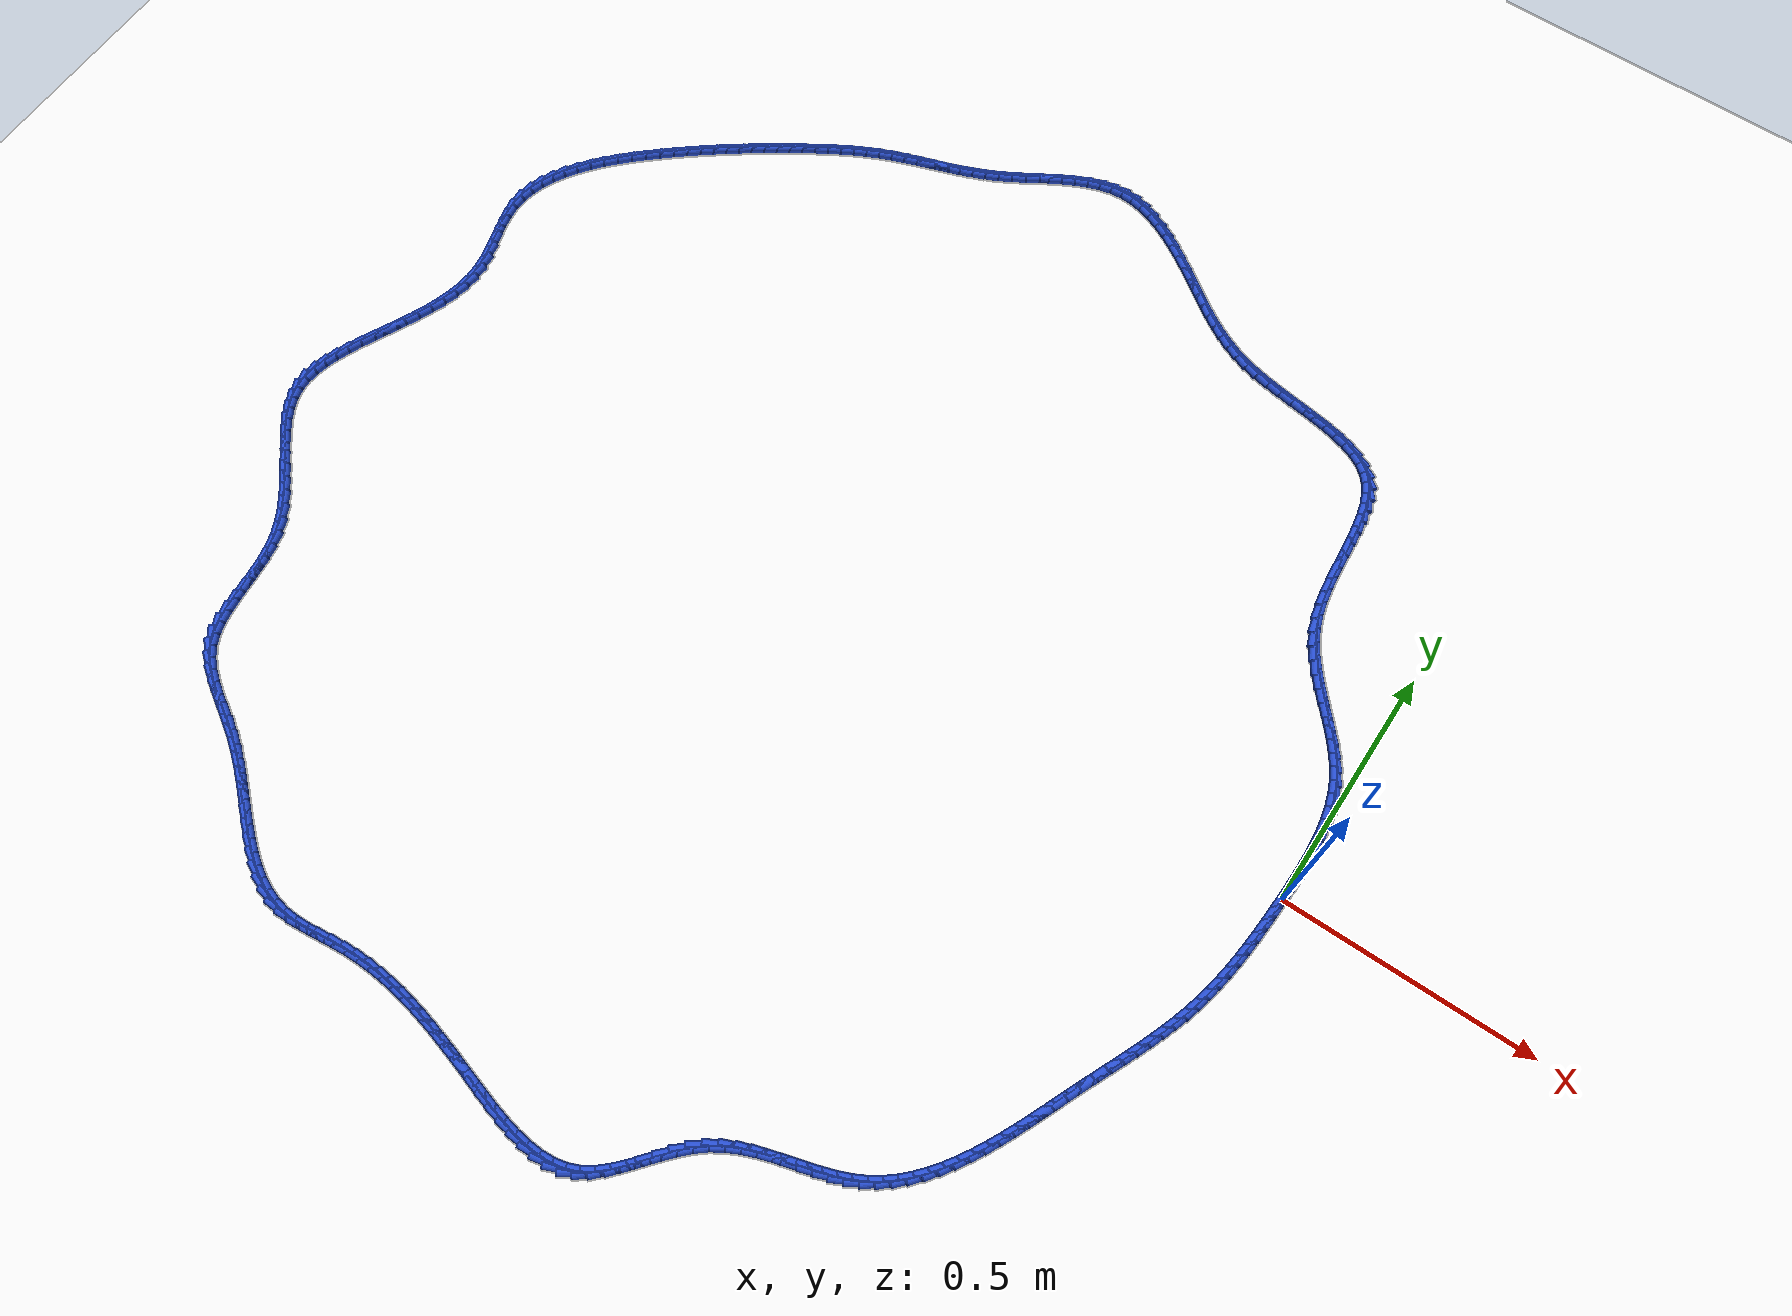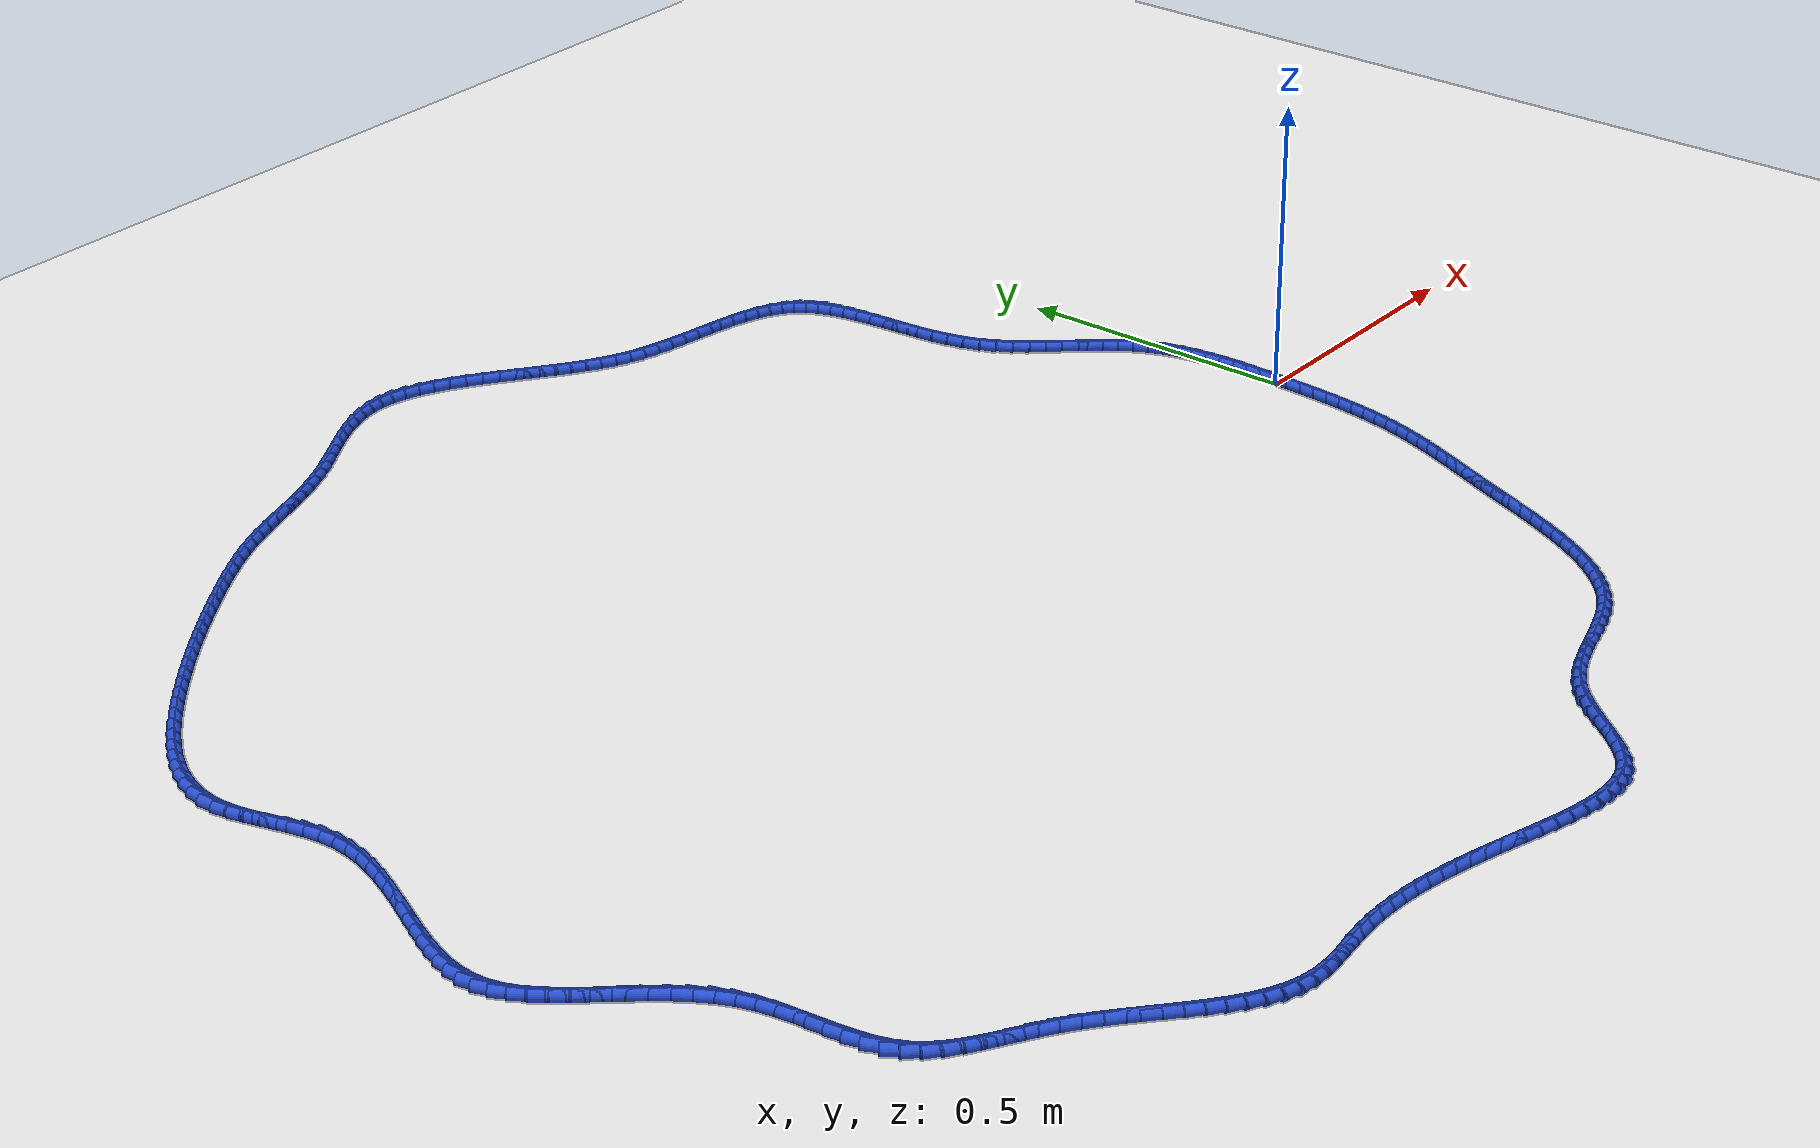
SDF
<sdf version="1.6">
 <world name="default">
  <light name="sun" type="directional">
   <pose>0 0 10 0 -0 0</pose>
   <diffuse>0.8 0.8 0.8 1</diffuse>
   <specular>0.2 0.2 0.2 1</specular>
   <attenuation>
    <range>1000</range>
    <constant>0.9</constant>
    <linear>0.01</linear>
    <quadratic>0.001</quadratic>
   </attenuation>
   <direction>-0.5 0.1 -0.9</direction>
  </light>
  <model name="ground_plane">
   <static>1</static>
   <link name="link">
    <collision name="collision">
     <geometry><plane><normal>0 0 1</normal><size>100 100</size></plane></geometry>
     <surface><friction><ode><mu>100</mu><mu2>50</mu2></ode></friction></surface>
    </collision>
    <visual name="visual">
     <cast_shadows>0</cast_shadows>
     <geometry><plane><normal>0 0 1</normal><size>100 100</size></plane></geometry>
     <material>
      <script><uri>file://media/materials/scripts/gazebo.material</uri><name>Gazebo/WhiteGlow</name></script>
     </material>
    </visual>
   </link>
  </model>
  <gravity>0 0 -9.8</gravity>
  <magnetic_field>6e-06 2.3e-05 -4.2e-05</magnetic_field>
  <atmosphere type="adiabatic"/>
  <physics name="default_physics" default="0" type="ode">
   <max_step_size>0.001</max_step_size>
   <real_time_factor>1</real_time_factor>
   <real_time_update_rate>1000</real_time_update_rate>
  </physics>
  <scene><ambient>0.4 0.4 0.4 1</ambient><background>0.7 0.7 0.7 1</background><shadows>1</shadows></scene>
  <spherical_coordinates>
   <surface_model>EARTH_WGS84</surface_model>
   <latitude_deg>0</latitude_deg>
   <longitude_deg>0</longitude_deg>
   <elevation>0</elevation>
   <heading_deg>0</heading_deg>
  </spherical_coordinates>
  <model name="line">
   <link name="link_0">
    <pose>1.734723475976807e-18 -3.469446951953614e-17 0.01 0 1.57 1.534499082581251</pose>
    <collision name="collision">
     <geometry><cylinder><radius>0.01</radius><length>0.08</length></cylinder></geometry>
    </collision>
    <visual name="visual">
     <material>
      <script><name>Gazebo/Blue</name><uri>file://media/materials/scripts/gazebo.material</uri></script>
     </material>
     <geometry><cylinder><radius>0.01</radius><length>0.08</length></cylinder></geometry>
    </visual>
   </link>
   <link name="link_1">
    <pose>0.0010244381826505077 0.028211184337771505 0.01 0 1.57 1.5508360316246745</pose>
    <collision name="collision">
     <geometry><cylinder><radius>0.01</radius><length>0.08</length></cylinder></geometry>
    </collision>
    <visual name="visual">
     <material>
      <script><name>Gazebo/Blue</name><uri>file://media/materials/scripts/gazebo.material</uri></script>
     </material>
     <geometry><cylinder><radius>0.01</radius><length>0.08</length></cylinder></geometry>
    </visual>
   </link>
   <link name="link_2">
    <pose>0.0015889900832004194 0.05649117312218792 0.01 0 1.57 -1.5654724552780257</pose>
    <collision name="collision">
     <geometry><cylinder><radius>0.01</radius><length>0.08</length></cylinder></geometry>
    </collision>
    <visual name="visual">
     <material>
      <script><name>Gazebo/Blue</name><uri>file://media/materials/scripts/gazebo.material</uri></script>
     </material>
     <geometry><cylinder><radius>0.01</radius><length>0.08</length></cylinder></geometry>
    </visual>
   </link>
   <link name="link_3">
    <pose>0.0014389059966526364 0.08468168600264829 0.01 0 1.57 -1.530754771913588</pose>
    <collision name="collision">
     <geometry><cylinder><radius>0.01</radius><length>0.08</length></cylinder></geometry>
    </collision>
    <visual name="visual">
     <material>
      <script><name>Gazebo/Blue</name><uri>file://media/materials/scripts/gazebo.material</uri></script>
     </material>
     <geometry><cylinder><radius>0.01</radius><length>0.08</length></cylinder></geometry>
    </visual>
   </link>
   <link name="link_4">
    <pose>0.0003194362180100542 0.11262444262855158 0.01 0 1.57 -1.4858925671162506</pose>
    <collision name="collision">
     <geometry><cylinder><radius>0.01</radius><length>0.08</length></cylinder></geometry>
    </collision>
    <visual name="visual">
     <material>
      <script><name>Gazebo/Blue</name><uri>file://media/materials/scripts/gazebo.material</uri></script>
     </material>
     <geometry><cylinder><radius>0.01</radius><length>0.08</length></cylinder></geometry>
    </visual>
   </link>
   <link name="link_5">
    <pose>-0.00202416895772443 0.14016116264929682 0.01 0 1.57 -1.4300152551584602</pose>
    <collision name="collision">
     <geometry><cylinder><radius>0.01</radius><length>0.08</length></cylinder></geometry>
    </collision>
    <visual name="visual">
     <material>
      <script><name>Gazebo/Blue</name><uri>file://media/materials/scripts/gazebo.material</uri></script>
     </material>
     <geometry><cylinder><radius>0.01</radius><length>0.08</length></cylinder></geometry>
    </visual>
   </link>
   <link name="link_6">
    <pose>-0.005846659235547922 0.167133565714283 0.01 0 1.57 -1.3622114532721696</pose>
    <collision name="collision">
     <geometry><cylinder><radius>0.01</radius><length>0.08</length></cylinder></geometry>
    </collision>
    <visual name="visual">
     <material>
      <script><name>Gazebo/Blue</name><uri>file://media/materials/scripts/gazebo.material</uri></script>
     </material>
     <geometry><cylinder><radius>0.01</radius><length>0.08</length></cylinder></geometry>
    </visual>
   </link>
   <link name="link_7">
    <pose>-0.01140278432045752 0.19338337147290913 0.01 0 1.57 -1.2817341484935918</pose>
    <collision name="collision">
     <geometry><cylinder><radius>0.01</radius><length>0.08</length></cylinder></geometry>
    </collision>
    <visual name="visual">
     <material>
      <script><name>Gazebo/Blue</name><uri>file://media/materials/scripts/gazebo.material</uri></script>
     </material>
     <geometry><cylinder><radius>0.01</radius><length>0.08</length></cylinder></geometry>
    </visual>
   </link>
   <link name="link_8">
    <pose>-0.01894729391745033 0.2187522995745742 0.01 0 1.57 -1.1883166431062484</pose>
    <collision name="collision">
     <geometry><cylinder><radius>0.01</radius><length>0.08</length></cylinder></geometry>
    </collision>
    <visual name="visual">
     <material>
      <script><name>Gazebo/Blue</name><uri>file://media/materials/scripts/gazebo.material</uri></script>
     </material>
     <geometry><cylinder><radius>0.01</radius><length>0.08</length></cylinder></geometry>
    </visual>
   </link>
   <link name="link_9">
    <pose>-0.02873493773152347 0.24308206966867724 0.01 0 1.57 -1.0850132831528254</pose>
    <collision name="collision">
     <geometry><cylinder><radius>0.01</radius><length>0.08</length></cylinder></geometry>
    </collision>
    <visual name="visual">
     <material>
      <script><name>Gazebo/Blue</name><uri>file://media/materials/scripts/gazebo.material</uri></script>
     </material>
     <geometry><cylinder><radius>0.01</radius><length>0.08</length></cylinder></geometry>
    </visual>
   </link>
   <link name="link_10">
    <pose>-0.04096515103989245 0.26624607289294405 0.01 0 1.57 -0.9937251131377034</pose>
    <collision name="collision">
     <geometry><cylinder><radius>0.01</radius><length>0.08</length></cylinder></geometry>
    </collision>
    <visual name="visual">
     <material>
      <script><name>Gazebo/Blue</name><uri>file://media/materials/scripts/gazebo.material</uri></script>
     </material>
     <geometry><cylinder><radius>0.01</radius><length>0.08</length></cylinder></geometry>
    </visual>
   </link>
   <link name="link_11">
    <pose>-0.05537552134493945 0.2883821414540246 0.01 0 1.57 -0.9253450676091585</pose>
    <collision name="collision">
     <geometry><cylinder><radius>0.01</radius><length>0.08</length></cylinder></geometry>
    </collision>
    <visual name="visual">
     <material>
      <script><name>Gazebo/Blue</name><uri>file://media/materials/scripts/gazebo.material</uri></script>
     </material>
     <geometry><cylinder><radius>0.01</radius><length>0.08</length></cylinder></geometry>
    </visual>
   </link>
   <link name="link_12">
    <pose>-0.07147389048696376 0.3097596534742844 0.01 0 1.57 -0.8793216079523238</pose>
    <collision name="collision">
     <geometry><cylinder><radius>0.01</radius><length>0.08</length></cylinder></geometry>
    </collision>
    <visual name="visual">
     <material>
      <script><name>Gazebo/Blue</name><uri>file://media/materials/scripts/gazebo.material</uri></script>
     </material>
     <geometry><cylinder><radius>0.01</radius><length>0.08</length></cylinder></geometry>
    </visual>
   </link>
   <link name="link_13">
    <pose>-0.08876642932128517 0.3306489438351731 0.01 0 1.57 -0.8545641053096079</pose>
    <collision name="collision">
     <geometry><cylinder><radius>0.01</radius><length>0.08</length></cylinder></geometry>
    </collision>
    <visual name="visual">
     <material>
      <script><name>Gazebo/Blue</name><uri>file://media/materials/scripts/gazebo.material</uri></script>
     </material>
     <geometry><cylinder><radius>0.01</radius><length>0.08</length></cylinder></geometry>
    </visual>
   </link>
   <link name="link_14">
    <pose>-0.10675930870322364 0.35132034741814083 0.01 0 1.57 -0.8501648669630004</pose>
    <collision name="collision">
     <geometry><cylinder><radius>0.01</radius><length>0.08</length></cylinder></geometry>
    </collision>
    <visual name="visual">
     <material>
      <script><name>Gazebo/Blue</name><uri>file://media/materials/scripts/gazebo.material</uri></script>
     </material>
     <geometry><cylinder><radius>0.01</radius><length>0.08</length></cylinder></geometry>
    </visual>
   </link>
   <link name="link_15">
    <pose>-0.12495869948809904 0.37204419910463715 0.01 0 1.57 -0.865683779056549</pose>
    <collision name="collision">
     <geometry><cylinder><radius>0.01</radius><length>0.08</length></cylinder></geometry>
    </collision>
    <visual name="visual">
     <material>
      <script><name>Gazebo/Blue</name><uri>file://media/materials/scripts/gazebo.material</uri></script>
     </material>
     <geometry><cylinder><radius>0.01</radius><length>0.08</length></cylinder></geometry>
    </visual>
   </link>
   <link name="link_16">
    <pose>-0.14287077253123137 0.39309083377611204 0.01 0 1.57 -0.9011728520162907</pose>
    <collision name="collision">
     <geometry><cylinder><radius>0.01</radius><length>0.08</length></cylinder></geometry>
    </collision>
    <visual name="visual">
     <material>
      <script><name>Gazebo/Blue</name><uri>file://media/materials/scripts/gazebo.material</uri></script>
     </material>
     <geometry><cylinder><radius>0.01</radius><length>0.08</length></cylinder></geometry>
    </visual>
   </link>
   <link name="link_17">
    <pose>-0.16000169868794042 0.4147305863140152 0.01 0 1.57 -0.9569840891715519</pose>
    <collision name="collision">
     <geometry><cylinder><radius>0.01</radius><length>0.08</length></cylinder></geometry>
    </collision>
    <visual name="visual">
     <material>
      <script><name>Gazebo/Blue</name><uri>file://media/materials/scripts/gazebo.material</uri></script>
     </material>
     <geometry><cylinder><radius>0.01</radius><length>0.08</length></cylinder></geometry>
    </visual>
   </link>
   <link name="link_18">
    <pose>-0.17585764881354612 0.4372337915997964 0.01 0 1.57 -1.033338891163884</pose>
    <collision name="collision">
     <geometry><cylinder><radius>0.01</radius><length>0.08</length></cylinder></geometry>
    </collision>
    <visual name="visual">
     <material>
      <script><name>Gazebo/Blue</name><uri>file://media/materials/scripts/gazebo.material</uri></script>
     </material>
     <geometry><cylinder><radius>0.01</radius><length>0.08</length></cylinder></geometry>
    </visual>
   </link>
   <link name="link_19">
    <pose>-0.1899447937633684 0.46087078451490565 0.01 0 1.57 -1.1296318845937405</pose>
    <collision name="collision">
     <geometry><cylinder><radius>0.01</radius><length>0.08</length></cylinder></geometry>
    </collision>
    <visual name="visual">
     <material>
      <script><name>Gazebo/Blue</name><uri>file://media/materials/scripts/gazebo.material</uri></script>
     </material>
     <geometry><cylinder><radius>0.01</radius><length>0.08</length></cylinder></geometry>
    </visual>
   </link>
   <link name="link_20">
    <pose>-0.20176930439272714 0.48591189994079254 0.01 0 1.57 -1.2389800258527615</pose>
    <collision name="collision">
     <geometry><cylinder><radius>0.01</radius><length>0.08</length></cylinder></geometry>
    </collision>
    <visual name="visual">
     <material>
      <script><name>Gazebo/Blue</name><uri>file://media/materials/scripts/gazebo.material</uri></script>
     </material>
     <geometry><cylinder><radius>0.01</radius><length>0.08</length></cylinder></geometry>
    </visual>
   </link>
   <link name="link_21">
    <pose>-0.2109489104038942 0.5125537769497239 0.01 0 1.57 -1.332416247217029</pose>
    <collision name="collision">
     <geometry><cylinder><radius>0.01</radius><length>0.08</length></cylinder></geometry>
    </collision>
    <visual name="visual">
     <material>
      <script><name>Gazebo/Blue</name><uri>file://media/materials/scripts/gazebo.material</uri></script>
     </material>
     <geometry><cylinder><radius>0.01</radius><length>0.08</length></cylinder></geometry>
    </visual>
   </link>
   <link name="link_22">
    <pose>-0.21775477456855927 0.5405613965239663 0.01 0 1.57 -1.4019504774807319</pose>
    <collision name="collision">
     <geometry><cylinder><radius>0.01</radius><length>0.08</length></cylinder></geometry>
    </collision>
    <visual name="visual">
     <material>
      <script><name>Gazebo/Blue</name><uri>file://media/materials/scripts/gazebo.material</uri></script>
     </material>
     <geometry><cylinder><radius>0.01</radius><length>0.08</length></cylinder></geometry>
    </visual>
   </link>
   <link name="link_23">
    <pose>-0.2226952458456503 0.5695430543763235 0.01 0 1.57 -1.4501635242684614</pose>
    <collision name="collision">
     <geometry><cylinder><radius>0.01</radius><length>0.08</length></cylinder></geometry>
    </collision>
    <visual name="visual">
     <material>
      <script><name>Gazebo/Blue</name><uri>file://media/materials/scripts/gazebo.material</uri></script>
     </material>
     <geometry><cylinder><radius>0.01</radius><length>0.08</length></cylinder></geometry>
    </visual>
   </link>
   <link name="link_24">
    <pose>-0.22627900726049407 0.599106825535232 0.01 0 1.57 -1.4791088921758047</pose>
    <collision name="collision">
     <geometry><cylinder><radius>0.01</radius><length>0.08</length></cylinder></geometry>
    </collision>
    <visual name="visual">
     <material>
      <script><name>Gazebo/Blue</name><uri>file://media/materials/scripts/gazebo.material</uri></script>
     </material>
     <geometry><cylinder><radius>0.01</radius><length>0.08</length></cylinder></geometry>
    </visual>
   </link>
   <link name="link_25">
    <pose>-0.229014741838417 0.6288607850291282 0.01 0 1.57 -1.4898833328625558</pose>
    <collision name="collision">
     <geometry><cylinder><radius>0.01</radius><length>0.08</length></cylinder></geometry>
    </collision>
    <visual name="visual">
     <material>
      <script><name>Gazebo/Blue</name><uri>file://media/materials/scripts/gazebo.material</uri></script>
     </material>
     <geometry><cylinder><radius>0.01</radius><length>0.08</length></cylinder></geometry>
    </visual>
   </link>
   <link name="link_26">
    <pose>-0.2314111326047456 0.658413007886449 0.01 0 1.57 -1.4824270266286634</pose>
    <collision name="collision">
     <geometry><cylinder><radius>0.01</radius><length>0.08</length></cylinder></geometry>
    </collision>
    <visual name="visual">
     <material>
      <script><name>Gazebo/Blue</name><uri>file://media/materials/scripts/gazebo.material</uri></script>
     </material>
     <geometry><cylinder><radius>0.01</radius><length>0.08</length></cylinder></geometry>
    </visual>
   </link>
   <link name="link_27">
    <pose>-0.23397686258480666 0.6873715691356306 0.01 0 1.57 -1.4553517194785355</pose>
    <collision name="collision">
     <geometry><cylinder><radius>0.01</radius><length>0.08</length></cylinder></geometry>
    </collision>
    <visual name="visual">
     <material>
      <script><name>Gazebo/Blue</name><uri>file://media/materials/scripts/gazebo.material</uri></script>
     </material>
     <geometry><cylinder><radius>0.01</radius><length>0.08</length></cylinder></geometry>
    </visual>
   </link>
   <link name="link_28">
    <pose>-0.2372206148039265 0.7153445438051097 0.01 0 1.57 -1.4057251979546244</pose>
    <collision name="collision">
     <geometry><cylinder><radius>0.01</radius><length>0.08</length></cylinder></geometry>
    </collision>
    <visual name="visual">
     <material>
      <script><name>Gazebo/Blue</name><uri>file://media/materials/scripts/gazebo.material</uri></script>
     </material>
     <geometry><cylinder><radius>0.01</radius><length>0.08</length></cylinder></geometry>
    </visual>
   </link>
   <link name="link_29">
    <pose>-0.2416510722874317 0.7419400069233227 0.01 0 1.57 -1.3288779182609405</pose>
    <collision name="collision">
     <geometry><cylinder><radius>0.01</radius><length>0.08</length></cylinder></geometry>
    </collision>
    <visual name="visual">
     <material>
      <script><name>Gazebo/Blue</name><uri>file://media/materials/scripts/gazebo.material</uri></script>
     </material>
     <geometry><cylinder><radius>0.01</radius><length>0.08</length></cylinder></geometry>
    </visual>
   </link>
   <link name="link_30">
    <pose>-0.24777691806064892 0.7667660335187063 0.01 0 1.57 -1.218591786880306</pose>
    <collision name="collision">
     <geometry><cylinder><radius>0.01</radius><length>0.08</length></cylinder></geometry>
    </collision>
    <visual name="visual">
     <material>
      <script><name>Gazebo/Blue</name><uri>file://media/materials/scripts/gazebo.material</uri></script>
     </material>
     <geometry><cylinder><radius>0.01</radius><length>0.08</length></cylinder></geometry>
    </visual>
   </link>
   <link name="link_31">
    <pose>-0.25610683514890464 0.7894306986196973 0.01 0 1.57 -1.0686629468953663</pose>
    <collision name="collision">
     <geometry><cylinder><radius>0.01</radius><length>0.08</length></cylinder></geometry>
    </collision>
    <visual name="visual">
     <material>
      <script><name>Gazebo/Blue</name><uri>file://media/materials/scripts/gazebo.material</uri></script>
     </material>
     <geometry><cylinder><radius>0.01</radius><length>0.08</length></cylinder></geometry>
    </visual>
   </link>
   <link name="link_32">
    <pose>-0.26714950657752545 0.8095420772547315 0.01 0 1.57 -0.8778828394717879</pose>
    <collision name="collision">
     <geometry><cylinder><radius>0.01</radius><length>0.08</length></cylinder></geometry>
    </collision>
    <visual name="visual">
     <material>
      <script><name>Gazebo/Blue</name><uri>file://media/materials/scripts/gazebo.material</uri></script>
     </material>
     <geometry><cylinder><radius>0.01</radius><length>0.08</length></cylinder></geometry>
    </visual>
   </link>
   <link name="link_33">
    <pose>-0.2814066606128743 0.8267142812399378 0.01 0 1.57 -0.6769066921869799</pose>
    <collision name="collision">
     <geometry><cylinder><radius>0.01</radius><length>0.08</length></cylinder></geometry>
    </collision>
    <visual name="visual">
     <material>
      <script><name>Gazebo/Blue</name><uri>file://media/materials/scripts/gazebo.material</uri></script>
     </material>
     <geometry><cylinder><radius>0.01</radius><length>0.08</length></cylinder></geometry>
    </visual>
   </link>
   <link name="link_34">
    <pose>-0.29902377279542647 0.8408706526727773 0.01 0 1.57 -0.5096522520865737</pose>
    <collision name="collision">
     <geometry><cylinder><radius>0.01</radius><length>0.08</length></cylinder></geometry>
    </collision>
    <visual name="visual">
     <material>
      <script><name>Gazebo/Blue</name><uri>file://media/materials/scripts/gazebo.material</uri></script>
     </material>
     <geometry><cylinder><radius>0.01</radius><length>0.08</length></cylinder></geometry>
    </visual>
   </link>
   <link name="link_35">
    <pose>-0.3196266241799483 0.8523856327170312 0.01 0 1.57 -0.3810423490504991</pose>
    <collision name="collision">
     <geometry><cylinder><radius>0.01</radius><length>0.08</length></cylinder></geometry>
    </collision>
    <visual name="visual">
     <material>
      <script><name>Gazebo/Blue</name><uri>file://media/materials/scripts/gazebo.material</uri></script>
     </material>
     <geometry><cylinder><radius>0.01</radius><length>0.08</length></cylinder></geometry>
    </visual>
   </link>
   <link name="link_36">
    <pose>-0.3427998845881352 0.8616693474232053 0.01 0 1.57 -0.2865260909454239</pose>
    <collision name="collision">
     <geometry><cylinder><radius>0.01</radius><length>0.08</length></cylinder></geometry>
    </collision>
    <visual name="visual">
     <material>
      <script><name>Gazebo/Blue</name><uri>file://media/materials/scripts/gazebo.material</uri></script>
     </material>
     <geometry><cylinder><radius>0.01</radius><length>0.08</length></cylinder></geometry>
    </visual>
   </link>
   <link name="link_37">
    <pose>-0.3681282238416823 0.8691319228418062 0.01 0 1.57 -0.2199511641202159</pose>
    <collision name="collision">
     <geometry><cylinder><radius>0.01</radius><length>0.08</length></cylinder></geometry>
    </collision>
    <visual name="visual">
     <material>
      <script><name>Gazebo/Blue</name><uri>file://media/materials/scripts/gazebo.material</uri></script>
     </material>
     <geometry><cylinder><radius>0.01</radius><length>0.08</length></cylinder></geometry>
    </visual>
   </link>
   <link name="link_38">
    <pose>-0.3951963117622856 0.8751834850233399 0.01 0 1.57 -0.17604608693882437</pose>
    <collision name="collision">
     <geometry><cylinder><radius>0.01</radius><length>0.08</length></cylinder></geometry>
    </collision>
    <visual name="visual">
     <material>
      <script><name>Gazebo/Blue</name><uri>file://media/materials/scripts/gazebo.material</uri></script>
     </material>
     <geometry><cylinder><radius>0.01</radius><length>0.08</length></cylinder></geometry>
    </visual>
   </link>
   <link name="link_39">
    <pose>-0.42358881817164007 0.8802341600183119 0.01 0 1.57 -0.15104788204637618</pose>
    <collision name="collision">
     <geometry><cylinder><radius>0.01</radius><length>0.08</length></cylinder></geometry>
    </collision>
    <visual name="visual">
     <material>
      <script><name>Gazebo/Blue</name><uri>file://media/materials/scripts/gazebo.material</uri></script>
     </material>
     <geometry><cylinder><radius>0.01</radius><length>0.08</length></cylinder></geometry>
    </visual>
   </link>
   <link name="link_40">
    <pose>-0.4528904128914413 0.8846940738772284 0.01 0 1.57 -0.14264688297909003</pose>
    <collision name="collision">
     <geometry><cylinder><radius>0.01</radius><length>0.08</length></cylinder></geometry>
    </collision>
    <visual name="visual">
     <material>
      <script><name>Gazebo/Blue</name><uri>file://media/materials/scripts/gazebo.material</uri></script>
     </material>
     <geometry><cylinder><radius>0.01</radius><length>0.08</length></cylinder></geometry>
    </visual>
   </link>
   <link name="link_41">
    <pose>-0.48268576574338456 0.8889733526505953 0.01 0 1.57 -0.1497967404922965</pose>
    <collision name="collision">
     <geometry><cylinder><radius>0.01</radius><length>0.08</length></cylinder></geometry>
    </collision>
    <visual name="visual">
     <material>
      <script><name>Gazebo/Blue</name><uri>file://media/materials/scripts/gazebo.material</uri></script>
     </material>
     <geometry><cylinder><radius>0.01</radius><length>0.08</length></cylinder></geometry>
    </visual>
   </link>
   <link name="link_42">
    <pose>-0.5125595465491654 0.8934821223889188 0.01 0 1.57 -0.17256996178403525</pose>
    <collision name="collision">
     <geometry><cylinder><radius>0.01</radius><length>0.08</length></cylinder></geometry>
    </collision>
    <visual name="visual">
     <material>
      <script><name>Gazebo/Blue</name><uri>file://media/materials/scripts/gazebo.material</uri></script>
     </material>
     <geometry><cylinder><radius>0.01</radius><length>0.08</length></cylinder></geometry>
    </visual>
   </link>
   <link name="link_43">
    <pose>-0.5420964251304792 0.8986305091427046 0.01 0 1.57 -0.21208929926445858</pose>
    <collision name="collision">
     <geometry><cylinder><radius>0.01</radius><length>0.08</length></cylinder></geometry>
    </collision>
    <visual name="visual">
     <material>
      <script><name>Gazebo/Blue</name><uri>file://media/materials/scripts/gazebo.material</uri></script>
     </material>
     <geometry><cylinder><radius>0.01</radius><length>0.08</length></cylinder></geometry>
    </visual>
   </link>
   <link name="link_44">
    <pose>-0.570881071309021 0.9048286389624587 0.01 0 1.57 -0.2704958997921498</pose>
    <collision name="collision">
     <geometry><cylinder><radius>0.01</radius><length>0.08</length></cylinder></geometry>
    </collision>
    <visual name="visual">
     <material>
      <script><name>Gazebo/Blue</name><uri>file://media/materials/scripts/gazebo.material</uri></script>
     </material>
     <geometry><cylinder><radius>0.01</radius><length>0.08</length></cylinder></geometry>
    </visual>
   </link>
   <link name="link_45">
    <pose>-0.5984981549372819 0.912486637869676 0.01 0 1.57 -0.3457831768912361</pose>
    <collision name="collision">
     <geometry><cylinder><radius>0.01</radius><length>0.08</length></cylinder></geometry>
    </collision>
    <visual name="visual">
     <material>
      <script><name>Gazebo/Blue</name><uri>file://media/materials/scripts/gazebo.material</uri></script>
     </material>
     <geometry><cylinder><radius>0.01</radius><length>0.08</length></cylinder></geometry>
    </visual>
   </link>
   <link name="link_46">
    <pose>-0.6246467507662243 0.9219068555345604 0.01 0 1.57 -0.41914388112311046</pose>
    <collision name="collision">
     <geometry><cylinder><radius>0.01</radius><length>0.08</length></cylinder></geometry>
    </collision>
    <visual name="visual">
     <material>
      <script><name>Gazebo/Blue</name><uri>file://media/materials/scripts/gazebo.material</uri></script>
     </material>
     <geometry><cylinder><radius>0.01</radius><length>0.08</length></cylinder></geometry>
    </visual>
   </link>
   <link name="link_47">
    <pose>-0.6494747182112038 0.9329688592614362 0.01 0 1.57 -0.4835445485795554</pose>
    <collision name="collision">
     <geometry><cylinder><radius>0.01</radius><length>0.08</length></cylinder></geometry>
    </collision>
    <visual name="visual">
     <material>
      <script><name>Gazebo/Blue</name><uri>file://media/materials/scripts/gazebo.material</uri></script>
     </material>
     <geometry><cylinder><radius>0.01</radius><length>0.08</length></cylinder></geometry>
    </visual>
   </link>
   <link name="link_48">
    <pose>-0.6732399466000702 0.945448561505404 0.01 0 1.57 -0.5371172157268679</pose>
    <collision name="collision">
     <geometry><cylinder><radius>0.01</radius><length>0.08</length></cylinder></geometry>
    </collision>
    <visual name="visual">
     <material>
      <script><name>Gazebo/Blue</name><uri>file://media/materials/scripts/gazebo.material</uri></script>
     </material>
     <geometry><cylinder><radius>0.01</radius><length>0.08</length></cylinder></geometry>
    </visual>
   </link>
   <link name="link_49">
    <pose>-0.6962003252606745 0.9591218747215653 0.01 0 1.57 -0.5786962889239656</pose>
    <collision name="collision">
     <geometry><cylinder><radius>0.01</radius><length>0.08</length></cylinder></geometry>
    </collision>
    <visual name="visual">
     <material>
      <script><name>Gazebo/Blue</name><uri>file://media/materials/scripts/gazebo.material</uri></script>
     </material>
     <geometry><cylinder><radius>0.01</radius><length>0.08</length></cylinder></geometry>
    </visual>
   </link>
   <link name="link_50">
    <pose>-0.7186137435208662 0.9737647113650202 0.01 0 1.57 -0.6077234779325693</pose>
    <collision name="collision">
     <geometry><cylinder><radius>0.01</radius><length>0.08</length></cylinder></geometry>
    </collision>
    <visual name="visual">
     <material>
      <script><name>Gazebo/Blue</name><uri>file://media/materials/scripts/gazebo.material</uri></script>
     </material>
     <geometry><cylinder><radius>0.01</radius><length>0.08</length></cylinder></geometry>
    </visual>
   </link>
   <link name="link_51">
    <pose>-0.7407380907084953 0.9891529838908697 0.01 0 1.57 -0.6240988171783313</pose>
    <collision name="collision">
     <geometry><cylinder><radius>0.01</radius><length>0.08</length></cylinder></geometry>
    </collision>
    <visual name="visual">
     <material>
      <script><name>Gazebo/Blue</name><uri>file://media/materials/scripts/gazebo.material</uri></script>
     </material>
     <geometry><cylinder><radius>0.01</radius><length>0.08</length></cylinder></geometry>
    </visual>
   </link>
   <link name="link_52">
    <pose>-0.7628312561514121 1.0050626047542146 0.01 0 1.57 -0.6280412069094072</pose>
    <collision name="collision">
     <geometry><cylinder><radius>0.01</radius><length>0.08</length></cylinder></geometry>
    </collision>
    <visual name="visual">
     <material>
      <script><name>Gazebo/Blue</name><uri>file://media/materials/scripts/gazebo.material</uri></script>
     </material>
     <geometry><cylinder><radius>0.01</radius><length>0.08</length></cylinder></geometry>
    </visual>
   </link>
   <link name="link_53">
    <pose>-0.7851511291774668 1.0212694864101555 0.01 0 1.57 -0.619992401983801</pose>
    <collision name="collision">
     <geometry><cylinder><radius>0.01</radius><length>0.08</length></cylinder></geometry>
    </collision>
    <visual name="visual">
     <material>
      <script><name>Gazebo/Blue</name><uri>file://media/materials/scripts/gazebo.material</uri></script>
     </material>
     <geometry><cylinder><radius>0.01</radius><length>0.08</length></cylinder></geometry>
    </visual>
   </link>
   <link name="link_54">
    <pose>-0.8079555991145095 1.0375495413137934 0.01 0 1.57 -0.6005393554842274</pose>
    <collision name="collision">
     <geometry><cylinder><radius>0.01</radius><length>0.08</length></cylinder></geometry>
    </collision>
    <visual name="visual">
     <material>
      <script><name>Gazebo/Blue</name><uri>file://media/materials/scripts/gazebo.material</uri></script>
     </material>
     <geometry><cylinder><radius>0.01</radius><length>0.08</length></cylinder></geometry>
    </visual>
   </link>
   <link name="link_55">
    <pose>-0.8314730181539275 1.0536573012162709 0.01 0 1.57 -0.5697730747402984</pose>
    <collision name="collision">
     <geometry><cylinder><radius>0.01</radius><length>0.08</length></cylinder></geometry>
    </collision>
    <visual name="visual">
     <material>
      <script><name>Gazebo/Blue</name><uri>file://media/materials/scripts/gazebo.material</uri></script>
     </material>
     <geometry><cylinder><radius>0.01</radius><length>0.08</length></cylinder></geometry>
    </visual>
   </link>
   <link name="link_56">
    <pose>-0.855684706038821 1.0691684813591624 0.01 0 1.57 -0.5267310126437706</pose>
    <collision name="collision">
     <geometry><cylinder><radius>0.01</radius><length>0.08</length></cylinder></geometry>
    </collision>
    <visual name="visual">
     <material>
      <script><name>Gazebo/Blue</name><uri>file://media/materials/scripts/gazebo.material</uri></script>
     </material>
     <geometry><cylinder><radius>0.01</radius><length>0.08</length></cylinder></geometry>
    </visual>
   </link>
   <link name="link_57">
    <pose>-0.8804489248943463 1.083569720695204 0.01 0 1.57 -0.469674578996793</pose>
    <collision name="collision">
     <geometry><cylinder><radius>0.01</radius><length>0.08</length></cylinder></geometry>
    </collision>
    <visual name="visual">
     <material>
      <script><name>Gazebo/Blue</name><uri>file://media/materials/scripts/gazebo.material</uri></script>
     </material>
     <geometry><cylinder><radius>0.01</radius><length>0.08</length></cylinder></geometry>
    </visual>
   </link>
   <link name="link_58">
    <pose>-0.9056230370623267 1.0963470068614178 0.01 0 1.57 -0.39608823904862245</pose>
    <collision name="collision">
     <geometry><cylinder><radius>0.01</radius><length>0.08</length></cylinder></geometry>
    </collision>
    <visual name="visual">
     <material>
      <script><name>Gazebo/Blue</name><uri>file://media/materials/scripts/gazebo.material</uri></script>
     </material>
     <geometry><cylinder><radius>0.01</radius><length>0.08</length></cylinder></geometry>
    </visual>
   </link>
   <link name="link_59">
    <pose>-0.9310644048845866 1.106986327494828 0.01 0 1.57 -0.30281260594155407</pose>
    <collision name="collision">
     <geometry><cylinder><radius>0.01</radius><length>0.08</length></cylinder></geometry>
    </collision>
    <visual name="visual">
     <material>
      <script><name>Gazebo/Blue</name><uri>file://media/materials/scripts/gazebo.material</uri></script>
     </material>
     <geometry><cylinder><radius>0.01</radius><length>0.08</length></cylinder></geometry>
    </visual>
   </link>
   <link name="link_60">
    <pose>-0.9566303907029502 1.114973670232458 0.01 0 1.57 -0.1865239989071952</pose>
    <collision name="collision">
     <geometry><cylinder><radius>0.01</radius><length>0.08</length></cylinder></geometry>
    </collision>
    <visual name="visual">
     <material>
      <script><name>Gazebo/Blue</name><uri>file://media/materials/scripts/gazebo.material</uri></script>
     </material>
     <geometry><cylinder><radius>0.01</radius><length>0.08</length></cylinder></geometry>
    </visual>
   </link>
   <link name="link_61">
    <pose>-0.9821783568592413 1.1197950227113316 0.01 0 1.57 -0.04500595836349071</pose>
    <collision name="collision">
     <geometry><cylinder><radius>0.01</radius><length>0.08</length></cylinder></geometry>
    </collision>
    <visual name="visual">
     <material>
      <script><name>Gazebo/Blue</name><uri>file://media/materials/scripts/gazebo.material</uri></script>
     </material>
     <geometry><cylinder><radius>0.01</radius><length>0.08</length></cylinder></geometry>
    </visual>
   </link>
   <link name="link_62">
    <pose>-1.0075660268549216 1.120938391212498 0.01 0 1.57 0.10803287013768177</pose>
    <collision name="collision">
     <geometry><cylinder><radius>0.01</radius><length>0.08</length></cylinder></geometry>
    </collision>
    <visual name="visual">
     <material>
      <script><name>Gazebo/Blue</name><uri>file://media/materials/scripts/gazebo.material</uri></script>
     </material>
     <geometry><cylinder><radius>0.01</radius><length>0.08</length></cylinder></geometry>
    </visual>
   </link>
   <link name="link_63">
    <pose>-1.032708339608371 1.1182115784381603 0.01 0 1.57 0.24081633196380592</pose>
    <collision name="collision">
     <geometry><cylinder><radius>0.01</radius><length>0.08</length></cylinder></geometry>
    </collision>
    <visual name="visual">
     <material>
      <script><name>Gazebo/Blue</name><uri>file://media/materials/scripts/gazebo.material</uri></script>
     </material>
     <geometry><cylinder><radius>0.01</radius><length>0.08</length></cylinder></geometry>
    </visual>
   </link>
   <link name="link_64">
    <pose>-1.0576394874435977 1.1120889349264704 0.01 0 1.57 0.3471244736066722</pose>
    <collision name="collision">
     <geometry><cylinder><radius>0.01</radius><length>0.08</length></cylinder></geometry>
    </collision>
    <visual name="visual">
     <material>
      <script><name>Gazebo/Blue</name><uri>file://media/materials/scripts/gazebo.material</uri></script>
     </material>
     <geometry><cylinder><radius>0.01</radius><length>0.08</length></cylinder></geometry>
    </visual>
   </link>
   <link name="link_65">
    <pose>-1.0824085718132321 1.10312814340527 0.01 0 1.57 0.4277673402619732</pose>
    <collision name="collision">
     <geometry><cylinder><radius>0.01</radius><length>0.08</length></cylinder></geometry>
    </collision>
    <visual name="visual">
     <material>
      <script><name>Gazebo/Blue</name><uri>file://media/materials/scripts/gazebo.material</uri></script>
     </material>
     <geometry><cylinder><radius>0.01</radius><length>0.08</length></cylinder></geometry>
    </visual>
   </link>
   <link name="link_66">
    <pose>-1.107064694169904 1.0918868866024027 0.01 0 1.57 0.48513823082255536</pose>
    <collision name="collision">
     <geometry><cylinder><radius>0.01</radius><length>0.08</length></cylinder></geometry>
    </collision>
    <visual name="visual">
     <material>
      <script><name>Gazebo/Blue</name><uri>file://media/materials/scripts/gazebo.material</uri></script>
     </material>
     <geometry><cylinder><radius>0.01</radius><length>0.08</length></cylinder></geometry>
    </visual>
   </link>
   <link name="link_67">
    <pose>-1.1316569559662435 1.0789228472457113 0.01 0 1.57 0.5217448392616452</pose>
    <collision name="collision">
     <geometry><cylinder><radius>0.01</radius><length>0.08</length></cylinder></geometry>
    </collision>
    <visual name="visual">
     <material>
      <script><name>Gazebo/Blue</name><uri>file://media/materials/scripts/gazebo.material</uri></script>
     </material>
     <geometry><cylinder><radius>0.01</radius><length>0.08</length></cylinder></geometry>
    </visual>
   </link>
   <link name="link_68">
    <pose>-1.1562344586548812 1.0647937080630392 0.01 0 1.57 0.5395062781494867</pose>
    <collision name="collision">
     <geometry><cylinder><radius>0.01</radius><length>0.08</length></cylinder></geometry>
    </collision>
    <visual name="visual">
     <material>
      <script><name>Gazebo/Blue</name><uri>file://media/materials/scripts/gazebo.material</uri></script>
     </material>
     <geometry><cylinder><radius>0.01</radius><length>0.08</length></cylinder></geometry>
    </visual>
   </link>
   <link name="link_69">
    <pose>-1.1808463036884471 1.0500571517822288 0.01 0 1.57 0.5394994722463647</pose>
    <collision name="collision">
     <geometry><cylinder><radius>0.01</radius><length>0.08</length></cylinder></geometry>
    </collision>
    <visual name="visual">
     <material>
      <script><name>Gazebo/Blue</name><uri>file://media/materials/scripts/gazebo.material</uri></script>
     </material>
     <geometry><cylinder><radius>0.01</radius><length>0.08</length></cylinder></geometry>
    </visual>
   </link>
   <link name="link_70">
    <pose>-1.2055415925195707 1.035270861131123 0.01 0 1.57 0.5219050378877268</pose>
    <collision name="collision">
     <geometry><cylinder><radius>0.01</radius><length>0.08</length></cylinder></geometry>
    </collision>
    <visual name="visual">
     <material>
      <script><name>Gazebo/Blue</name><uri>file://media/materials/scripts/gazebo.material</uri></script>
     </material>
     <geometry><cylinder><radius>0.01</radius><length>0.08</length></cylinder></geometry>
    </visual>
   </link>
   <link name="link_71">
    <pose>-1.2303694266008836 1.0209925188375653 0.01 0 1.57 0.4860750051244656</pose>
    <collision name="collision">
     <geometry><cylinder><radius>0.01</radius><length>0.08</length></cylinder></geometry>
    </collision>
    <visual name="visual">
     <material>
      <script><name>Gazebo/Blue</name><uri>file://media/materials/scripts/gazebo.material</uri></script>
     </material>
     <geometry><cylinder><radius>0.01</radius><length>0.08</length></cylinder></geometry>
    </visual>
   </link>
   <link name="link_72">
    <pose>-1.2553787607886444 1.0077786623940896 0.01 0 1.57 0.43884690385221387</pose>
    <collision name="collision">
     <geometry><cylinder><radius>0.01</radius><length>0.08</length></cylinder></geometry>
    </collision>
    <visual name="visual">
     <material>
      <script><name>Gazebo/Blue</name><uri>file://media/materials/scripts/gazebo.material</uri></script>
     </material>
     <geometry><cylinder><radius>0.01</radius><length>0.08</length></cylinder></geometry>
    </visual>
   </link>
   <link name="link_73">
    <pose>-1.2805878753173927 0.9959461940297539 0.01 0 1.57 0.398182398537582</pose>
    <collision name="collision">
     <geometry><cylinder><radius>0.01</radius><length>0.08</length></cylinder></geometry>
    </collision>
    <visual name="visual">
     <material>
      <script><name>Gazebo/Blue</name><uri>file://media/materials/scripts/gazebo.material</uri></script>
     </material>
     <geometry><cylinder><radius>0.01</radius><length>0.08</length></cylinder></geometry>
    </visual>
   </link>
   <link name="link_74">
    <pose>-1.3059468085409323 0.9852788990139479 0.01 0 1.57 0.36723988304731636</pose>
    <collision name="collision">
     <geometry><cylinder><radius>0.01</radius><length>0.08</length></cylinder></geometry>
    </collision>
    <visual name="visual">
     <material>
      <script><name>Gazebo/Blue</name><uri>file://media/materials/scripts/gazebo.material</uri></script>
     </material>
     <geometry><cylinder><radius>0.01</radius><length>0.08</length></cylinder></geometry>
    </visual>
   </link>
   <link name="link_75">
    <pose>-1.3313963957325856 0.9754886666156549 0.01 0 1.57 0.3465312504538547</pose>
    <collision name="collision">
     <geometry><cylinder><radius>0.01</radius><length>0.08</length></cylinder></geometry>
    </collision>
    <visual name="visual">
     <material>
      <script><name>Gazebo/Blue</name><uri>file://media/materials/scripts/gazebo.material</uri></script>
     </material>
     <geometry><cylinder><radius>0.01</radius><length>0.08</length></cylinder></geometry>
    </visual>
   </link>
   <link name="link_76">
    <pose>-1.356877472165676 0.9662873861038577 0.01 0 1.57 0.3363860062045474</pose>
    <collision name="collision">
     <geometry><cylinder><radius>0.01</radius><length>0.08</length></cylinder></geometry>
    </collision>
    <visual name="visual">
     <material>
      <script><name>Gazebo/Blue</name><uri>file://media/materials/scripts/gazebo.material</uri></script>
     </material>
     <geometry><cylinder><radius>0.01</radius><length>0.08</length></cylinder></geometry>
    </visual>
   </link>
   <link name="link_77">
    <pose>-1.3823308731135262 0.9573869467475392 0.01 0 1.57 0.337005352391431</pose>
    <collision name="collision">
     <geometry><cylinder><radius>0.01</radius><length>0.08</length></cylinder></geometry>
    </collision>
    <visual name="visual">
     <material>
      <script><name>Gazebo/Blue</name><uri>file://media/materials/scripts/gazebo.material</uri></script>
     </material>
     <geometry><cylinder><radius>0.01</radius><length>0.08</length></cylinder></geometry>
    </visual>
   </link>
   <link name="link_78">
    <pose>-1.4076974338494592 0.9484992378156825 0.01 0 1.57 0.3484900497054058</pose>
    <collision name="collision">
     <geometry><cylinder><radius>0.01</radius><length>0.08</length></cylinder></geometry>
    </collision>
    <visual name="visual">
     <material>
      <script><name>Gazebo/Blue</name><uri>file://media/materials/scripts/gazebo.material</uri></script>
     </material>
     <geometry><cylinder><radius>0.01</radius><length>0.08</length></cylinder></geometry>
    </visual>
   </link>
   <link name="link_79">
    <pose>-1.432917989646798 0.9393361485772707 0.01 0 1.57 0.37083484582573073</pose>
    <collision name="collision">
     <geometry><cylinder><radius>0.01</radius><length>0.08</length></cylinder></geometry>
    </collision>
    <visual name="visual">
     <material>
      <script><name>Gazebo/Blue</name><uri>file://media/materials/scripts/gazebo.material</uri></script>
     </material>
     <geometry><cylinder><radius>0.01</radius><length>0.08</length></cylinder></geometry>
    </visual>
   </link>
   <link name="link_80">
    <pose>-1.4579333757788657 0.9296095683012866 0.01 0 1.57 0.4038705799674041</pose>
    <collision name="collision">
     <geometry><cylinder><radius>0.01</radius><length>0.08</length></cylinder></geometry>
    </collision>
    <visual name="visual">
     <material>
      <script><name>Gazebo/Blue</name><uri>file://media/materials/scripts/gazebo.material</uri></script>
     </material>
     <geometry><cylinder><radius>0.01</radius><length>0.08</length></cylinder></geometry>
    </visual>
   </link>
   <link name="link_81">
    <pose>-1.4826844880903323 0.9190318541826664 0.01 0 1.57 0.4430424385501242</pose>
    <collision name="collision">
     <geometry><cylinder><radius>0.01</radius><length>0.08</length></cylinder></geometry>
    </collision>
    <visual name="visual">
     <material>
      <script><name>Gazebo/Blue</name><uri>file://media/materials/scripts/gazebo.material</uri></script>
     </material>
     <geometry><cylinder><radius>0.01</radius><length>0.08</length></cylinder></geometry>
    </visual>
   </link>
   <link name="link_82">
    <pose>-1.5071275238153965 0.9074335697565526 0.01 0 1.57 0.47849826891946695</pose>
    <collision name="collision">
     <geometry><cylinder><radius>0.01</radius><length>0.08</length></cylinder></geometry>
    </collision>
    <visual name="visual">
     <material>
      <script><name>Gazebo/Blue</name><uri>file://media/materials/scripts/gazebo.material</uri></script>
     </material>
     <geometry><cylinder><radius>0.01</radius><length>0.08</length></cylinder></geometry>
    </visual>
   </link>
   <link name="link_83">
    <pose>-1.5312541151043764 0.8949190204781869 0.01 0 1.57 0.5090824668394416</pose>
    <collision name="collision">
     <geometry><cylinder><radius>0.01</radius><length>0.08</length></cylinder></geometry>
    </collision>
    <visual name="visual">
     <material>
      <script><name>Gazebo/Blue</name><uri>file://media/materials/scripts/gazebo.material</uri></script>
     </material>
     <geometry><cylinder><radius>0.01</radius><length>0.08</length></cylinder></geometry>
    </visual>
   </link>
   <link name="link_84">
    <pose>-1.555060896109739 0.8816311532847909 0.01 0 1.57 0.5350189812152231</pose>
    <collision name="collision">
     <geometry><cylinder><radius>0.01</radius><length>0.08</length></cylinder></geometry>
    </collision>
    <visual name="visual">
     <material>
      <script><name>Gazebo/Blue</name><uri>file://media/materials/scripts/gazebo.material</uri></script>
     </material>
     <geometry><cylinder><radius>0.01</radius><length>0.08</length></cylinder></geometry>
    </visual>
   </link>
   <link name="link_85">
    <pose>-1.5785445009839503 0.8677129151135854 0.01 0 1.57 0.5565004118699376</pose>
    <collision name="collision">
     <geometry><cylinder><radius>0.01</radius><length>0.08</length></cylinder></geometry>
    </collision>
    <visual name="visual">
     <material>
      <script><name>Gazebo/Blue</name><uri>file://media/materials/scripts/gazebo.material</uri></script>
     </material>
     <geometry><cylinder><radius>0.01</radius><length>0.08</length></cylinder></geometry>
    </visual>
   </link>
   <link name="link_86">
    <pose>-1.6017015638794763 0.8533072529017917 0.01 0 1.57 0.5736754842337437</pose>
    <collision name="collision">
     <geometry><cylinder><radius>0.01</radius><length>0.08</length></cylinder></geometry>
    </collision>
    <visual name="visual">
     <material>
      <script><name>Gazebo/Blue</name><uri>file://media/materials/scripts/gazebo.material</uri></script>
     </material>
     <geometry><cylinder><radius>0.01</radius><length>0.08</length></cylinder></geometry>
    </visual>
   </link>
   <link name="link_87">
    <pose>-1.6245287189487843 0.8385571135866317 0.01 0 1.57 0.5866394132417062</pose>
    <collision name="collision">
     <geometry><cylinder><radius>0.01</radius><length>0.08</length></cylinder></geometry>
    </collision>
    <visual name="visual">
     <material>
      <script><name>Gazebo/Blue</name><uri>file://media/materials/scripts/gazebo.material</uri></script>
     </material>
     <geometry><cylinder><radius>0.01</radius><length>0.08</length></cylinder></geometry>
    </visual>
   </link>
   <link name="link_88">
    <pose>-1.6470226003443407 0.8236054441053265 0.01 0 1.57 0.5961312622181127</pose>
    <collision name="collision">
     <geometry><cylinder><radius>0.01</radius><length>0.08</length></cylinder></geometry>
    </collision>
    <visual name="visual">
     <material>
      <script><name>Gazebo/Blue</name><uri>file://media/materials/scripts/gazebo.material</uri></script>
     </material>
     <geometry><cylinder><radius>0.01</radius><length>0.08</length></cylinder></geometry>
    </visual>
   </link>
   <link name="link_89">
    <pose>-1.6691882941673888 0.80856663486908 0.01 0 1.57 0.6057436194269661</pose>
    <collision name="collision">
     <geometry><cylinder><radius>0.01</radius><length>0.08</length></cylinder></geometry>
    </collision>
    <visual name="visual">
     <material>
      <script><name>Gazebo/Blue</name><uri>file://media/materials/scripts/gazebo.material</uri></script>
     </material>
     <geometry><cylinder><radius>0.01</radius><length>0.08</length></cylinder></geometry>
    </visual>
   </link>
   <link name="link_90">
    <pose>-1.6910743197654523 0.7934083287566399 0.01 0 1.57 0.6165563024757809</pose>
    <collision name="collision">
     <geometry><cylinder><radius>0.01</radius><length>0.08</length></cylinder></geometry>
    </collision>
    <visual name="visual">
     <material>
      <script><name>Gazebo/Blue</name><uri>file://media/materials/scripts/gazebo.material</uri></script>
     </material>
     <geometry><cylinder><radius>0.01</radius><length>0.08</length></cylinder></geometry>
    </visual>
   </link>
   <link name="link_91">
    <pose>-1.7127431093770857 0.7780511612825145 0.01 0 1.57 0.6284579848128597</pose>
    <collision name="collision">
     <geometry><cylinder><radius>0.01</radius><length>0.08</length></cylinder></geometry>
    </collision>
    <visual name="visual">
     <material>
      <script><name>Gazebo/Blue</name><uri>file://media/materials/scripts/gazebo.material</uri></script>
     </material>
     <geometry><cylinder><radius>0.01</radius><length>0.08</length></cylinder></geometry>
    </visual>
   </link>
   <link name="link_92">
    <pose>-1.7342571015525952 0.7624157466357496 0.01 0 1.57 0.6413112505708879</pose>
    <collision name="collision">
     <geometry><cylinder><radius>0.01</radius><length>0.08</length></cylinder></geometry>
    </collision>
    <visual name="visual">
     <material>
      <script><name>Gazebo/Blue</name><uri>file://media/materials/scripts/gazebo.material</uri></script>
     </material>
     <geometry><cylinder><radius>0.01</radius><length>0.08</length></cylinder></geometry>
    </visual>
   </link>
   <link name="link_93">
    <pose>-1.7556787348422869 0.7464226990053918 0.01 0 1.57 0.6549581235944474</pose>
    <collision name="collision">
     <geometry><cylinder><radius>0.01</radius><length>0.08</length></cylinder></geometry>
    </collision>
    <visual name="visual">
     <material>
      <script><name>Gazebo/Blue</name><uri>file://media/materials/scripts/gazebo.material</uri></script>
     </material>
     <geometry><cylinder><radius>0.01</radius><length>0.08</length></cylinder></geometry>
    </visual>
   </link>
   <link name="link_94">
    <pose>-1.7770704477964672 0.7299926325804869 0.01 0 1.57 0.6692262428386655</pose>
    <collision name="collision">
     <geometry><cylinder><radius>0.01</radius><length>0.08</length></cylinder></geometry>
    </collision>
    <visual name="visual">
     <material>
      <script><name>Gazebo/Blue</name><uri>file://media/materials/scripts/gazebo.material</uri></script>
     </material>
     <geometry><cylinder><radius>0.01</radius><length>0.08</length></cylinder></geometry>
    </visual>
   </link>
   <link name="link_95">
    <pose>-1.7984946789654421 0.7130461615500807 0.01 0 1.57 0.6839357194155656</pose>
    <collision name="collision">
     <geometry><cylinder><radius>0.01</radius><length>0.08</length></cylinder></geometry>
    </collision>
    <visual name="visual">
     <material>
      <script><name>Gazebo/Blue</name><uri>file://media/materials/scripts/gazebo.material</uri></script>
     </material>
     <geometry><cylinder><radius>0.01</radius><length>0.08</length></cylinder></geometry>
    </visual>
   </link>
   <link name="link_96">
    <pose>-1.820013866899518 0.69550390010322 0.01 0 1.57 0.6989061182299622</pose>
    <collision name="collision">
     <geometry><cylinder><radius>0.01</radius><length>0.08</length></cylinder></geometry>
    </collision>
    <visual name="visual">
     <material>
      <script><name>Gazebo/Blue</name><uri>file://media/materials/scripts/gazebo.material</uri></script>
     </material>
     <geometry><cylinder><radius>0.01</radius><length>0.08</length></cylinder></geometry>
    </visual>
   </link>
   <link name="link_97">
    <pose>-1.841690450149002 0.6772864624289505 0.01 0 1.57 0.7141485711446259</pose>
    <collision name="collision">
     <geometry><cylinder><radius>0.01</radius><length>0.08</length></cylinder></geometry>
    </collision>
    <visual name="visual">
     <material>
      <script><name>Gazebo/Blue</name><uri>file://media/materials/scripts/gazebo.material</uri></script>
     </material>
     <geometry><cylinder><radius>0.01</radius><length>0.08</length></cylinder></geometry>
    </visual>
   </link>
   <link name="link_98">
    <pose>-1.8635743801478564 0.6583181719075503 0.01 0 1.57 0.7326440340805234</pose>
    <collision name="collision">
     <geometry><cylinder><radius>0.01</radius><length>0.08</length></cylinder></geometry>
    </collision>
    <visual name="visual">
     <material>
      <script><name>Gazebo/Blue</name><uri>file://media/materials/scripts/gazebo.material</uri></script>
     </material>
     <geometry><cylinder><radius>0.01</radius><length>0.08</length></cylinder></geometry>
    </visual>
   </link>
   <link name="link_99">
    <pose>-1.8855074759100012 0.6385851758765901 0.01 0 1.57 0.7571074471507236</pose>
    <collision name="collision">
     <geometry><cylinder><radius>0.01</radius><length>0.08</length></cylinder></geometry>
    </collision>
    <visual name="visual">
     <material>
      <script><name>Gazebo/Blue</name><uri>file://media/materials/scripts/gazebo.material</uri></script>
     </material>
     <geometry><cylinder><radius>0.01</radius><length>0.08</length></cylinder></geometry>
    </visual>
   </link>
   <link name="link_100">
    <pose>-1.9071596982966623 0.6181246706697107 0.01 0 1.57 0.7880798289410872</pose>
    <collision name="collision">
     <geometry><cylinder><radius>0.01</radius><length>0.08</length></cylinder></geometry>
    </collision>
    <visual name="visual">
     <material>
      <script><name>Gazebo/Blue</name><uri>file://media/materials/scripts/gazebo.material</uri></script>
     </material>
     <geometry><cylinder><radius>0.01</radius><length>0.08</length></cylinder></geometry>
    </visual>
   </link>
   <link name="link_101">
    <pose>-1.9281958594137687 0.5969753820143272 0.01 0 1.57 0.8263079932634801</pose>
    <collision name="collision">
     <geometry><cylinder><radius>0.01</radius><length>0.08</length></cylinder></geometry>
    </collision>
    <visual name="visual">
     <material>
      <script><name>Gazebo/Blue</name><uri>file://media/materials/scripts/gazebo.material</uri></script>
     </material>
     <geometry><cylinder><radius>0.01</radius><length>0.08</length></cylinder></geometry>
    </visual>
   </link>
   <link name="link_102">
    <pose>-1.9482807713672472 0.5751760356378549 0.01 0 1.57 0.8728300612827734</pose>
    <collision name="collision">
     <geometry><cylinder><radius>0.01</radius><length>0.08</length></cylinder></geometry>
    </collision>
    <visual name="visual">
     <material>
      <script><name>Gazebo/Blue</name><uri>file://media/materials/scripts/gazebo.material</uri></script>
     </material>
     <geometry><cylinder><radius>0.01</radius><length>0.08</length></cylinder></geometry>
    </visual>
   </link>
   <link name="link_103">
    <pose>-1.9670792462630262 0.5527653572677094 0.01 0 1.57 0.9289852198765904</pose>
    <collision name="collision">
     <geometry><cylinder><radius>0.01</radius><length>0.08</length></cylinder></geometry>
    </collision>
    <visual name="visual">
     <material>
      <script><name>Gazebo/Blue</name><uri>file://media/materials/scripts/gazebo.material</uri></script>
     </material>
     <geometry><cylinder><radius>0.01</radius><length>0.08</length></cylinder></geometry>
    </visual>
   </link>
   <link name="link_104">
    <pose>-1.9842560962070352 0.5297820726313058 0.01 0 1.57 0.9964001485506433</pose>
    <collision name="collision">
     <geometry><cylinder><radius>0.01</radius><length>0.08</length></cylinder></geometry>
    </collision>
    <visual name="visual">
     <material>
      <script><name>Gazebo/Blue</name><uri>file://media/materials/scripts/gazebo.material</uri></script>
     </material>
     <geometry><cylinder><radius>0.01</radius><length>0.08</length></cylinder></geometry>
    </visual>
   </link>
   <link name="link_105">
    <pose>-1.9994761333052007 0.5062649074560599 0.01 0 1.57 1.0769090169903641</pose>
    <collision name="collision">
     <geometry><cylinder><radius>0.01</radius><length>0.08</length></cylinder></geometry>
    </collision>
    <visual name="visual">
     <material>
      <script><name>Gazebo/Blue</name><uri>file://media/materials/scripts/gazebo.material</uri></script>
     </material>
     <geometry><cylinder><radius>0.01</radius><length>0.08</length></cylinder></geometry>
    </visual>
   </link>
   <link name="link_106">
    <pose>-2.012404169663452 0.48225258746938654 0.01 0 1.57 1.1723357941536177</pose>
    <collision name="collision">
     <geometry><cylinder><radius>0.01</radius><length>0.08</length></cylinder></geometry>
    </collision>
    <visual name="visual">
     <material>
      <script><name>Gazebo/Blue</name><uri>file://media/materials/scripts/gazebo.material</uri></script>
     </material>
     <geometry><cylinder><radius>0.01</radius><length>0.08</length></cylinder></geometry>
    </visual>
   </link>
   <link name="link_107">
    <pose>-2.022705017387717 0.45778383839870124 0.01 0 1.57 1.2840450705789492</pose>
    <collision name="collision">
     <geometry><cylinder><radius>0.01</radius><length>0.08</length></cylinder></geometry>
    </collision>
    <visual name="visual">
     <material>
      <script><name>Gazebo/Blue</name><uri>file://media/materials/scripts/gazebo.material</uri></script>
     </material>
     <geometry><cylinder><radius>0.01</radius><length>0.08</length></cylinder></geometry>
    </visual>
   </link>
   <link name="link_108">
    <pose>-2.0300434885839236 0.4328973859714193 0.01 0 1.57 1.4122013469662544</pose>
    <collision name="collision">
     <geometry><cylinder><radius>0.01</radius><length>0.08</length></cylinder></geometry>
    </collision>
    <visual name="visual">
     <material>
      <script><name>Gazebo/Blue</name><uri>file://media/materials/scripts/gazebo.material</uri></script>
     </material>
     <geometry><cylinder><radius>0.01</radius><length>0.08</length></cylinder></geometry>
    </visual>
   </link>
   <link name="link_109">
    <pose>-2.034084395358 0.40763195591495627 0.01 0 1.57 1.5548562515610727</pose>
    <collision name="collision">
     <geometry><cylinder><radius>0.01</radius><length>0.08</length></cylinder></geometry>
    </collision>
    <visual name="visual">
     <material>
      <script><name>Gazebo/Blue</name><uri>file://media/materials/scripts/gazebo.material</uri></script>
     </material>
     <geometry><cylinder><radius>0.01</radius><length>0.08</length></cylinder></geometry>
    </visual>
   </link>
   <link name="link_110">
    <pose>-2.0344925864323202 0.38202627364129293 0.01 0 1.57 -1.4457102988363895</pose>
    <collision name="collision">
     <geometry><cylinder><radius>0.01</radius><length>0.08</length></cylinder></geometry>
    </collision>
    <visual name="visual">
     <material>
      <script><name>Gazebo/Blue</name><uri>file://media/materials/scripts/gazebo.material</uri></script>
     </material>
     <geometry><cylinder><radius>0.01</radius><length>0.08</length></cylinder></geometry>
    </visual>
   </link>
   <link name="link_111">
    <pose>-2.0312346217600123 0.35611646545508485 0.01 0 1.57 -1.3482895992699346</pose>
    <collision name="collision">
     <geometry><cylinder><radius>0.01</radius><length>0.08</length></cylinder></geometry>
    </collision>
    <visual name="visual">
     <material>
      <script><name>Gazebo/Blue</name><uri>file://media/materials/scripts/gazebo.material</uri></script>
     </material>
     <geometry><cylinder><radius>0.01</radius><length>0.08</length></cylinder></geometry>
    </visual>
   </link>
   <link name="link_112">
    <pose>-2.0253098018199336 0.32992976106320687 0.01 0 1.57 -1.2988797099758886</pose>
    <collision name="collision">
     <geometry><cylinder><radius>0.01</radius><length>0.08</length></cylinder></geometry>
    </collision>
    <visual name="visual">
     <material>
      <script><name>Gazebo/Blue</name><uri>file://media/materials/scripts/gazebo.material</uri></script>
     </material>
     <geometry><cylinder><radius>0.01</radius><length>0.08</length></cylinder></geometry>
    </visual>
   </link>
   <link name="link_113">
    <pose>-2.017938212422154 0.30349148820564165 0.01 0 1.57 -1.293195786567322</pose>
    <collision name="collision">
     <geometry><cylinder><radius>0.01</radius><length>0.08</length></cylinder></geometry>
    </collision>
    <visual name="visual">
     <material>
      <script><name>Gazebo/Blue</name><uri>file://media/materials/scripts/gazebo.material</uri></script>
     </material>
     <geometry><cylinder><radius>0.01</radius><length>0.08</length></cylinder></geometry>
    </visual>
   </link>
   <link name="link_114">
    <pose>-2.010339939376748 0.27682697462237227 0.01 0 1.57 -1.3297271415914858</pose>
    <collision name="collision">
     <geometry><cylinder><radius>0.01</radius><length>0.08</length></cylinder></geometry>
    </collision>
    <visual name="visual">
     <material>
      <script><name>Gazebo/Blue</name><uri>file://media/materials/scripts/gazebo.material</uri></script>
     </material>
     <geometry><cylinder><radius>0.01</radius><length>0.08</length></cylinder></geometry>
    </visual>
   </link>
   <link name="link_115">
    <pose>-2.003735068493786 0.24996154805338142 0.01 0 1.57 -1.4098046401773754</pose>
    <collision name="collision">
     <geometry><cylinder><radius>0.01</radius><length>0.08</length></cylinder></geometry>
    </collision>
    <visual name="visual">
     <material>
      <script><name>Gazebo/Blue</name><uri>file://media/materials/scripts/gazebo.material</uri></script>
     </material>
     <geometry><cylinder><radius>0.01</radius><length>0.08</length></cylinder></geometry>
    </visual>
   </link>
   <link name="link_116">
    <pose>-1.9993436855833422 0.22292053623865218 0.01 0 1.57 -1.5324261111794735</pose>
    <collision name="collision">
     <geometry><cylinder><radius>0.01</radius><length>0.08</length></cylinder></geometry>
    </collision>
    <visual name="visual">
     <material>
      <script><name>Gazebo/Blue</name><uri>file://media/materials/scripts/gazebo.material</uri></script>
     </material>
     <geometry><cylinder><radius>0.01</radius><length>0.08</length></cylinder></geometry>
    </visual>
   </link>
   <link name="link_117">
    <pose>-1.99829988942325 0.195730596282614 0.01 0 1.57 1.4814622633433203</pose>
    <collision name="collision">
     <geometry><cylinder><radius>0.01</radius><length>0.08</length></cylinder></geometry>
    </collision>
    <visual name="visual">
     <material>
      <script><name>Gazebo/Blue</name><uri>file://media/materials/scripts/gazebo.material</uri></script>
     </material>
     <geometry><cylinder><radius>0.01</radius><length>0.08</length></cylinder></geometry>
    </visual>
   </link>
   <link name="link_118">
    <pose>-2.000744936746869 0.1684337346846061 0.01 0 1.57 1.374546579074611</pose>
    <collision name="collision">
     <geometry><cylinder><radius>0.01</radius><length>0.08</length></cylinder></geometry>
    </collision>
    <visual name="visual">
     <material>
      <script><name>Gazebo/Blue</name><uri>file://media/materials/scripts/gazebo.material</uri></script>
     </material>
     <geometry><cylinder><radius>0.01</radius><length>0.08</length></cylinder></geometry>
    </visual>
   </link>
   <link name="link_119">
    <pose>-2.0061827350851695 0.14108181139916473 0.01 0 1.57 1.2888411445170007</pose>
    <collision name="collision">
     <geometry><cylinder><radius>0.01</radius><length>0.08</length></cylinder></geometry>
    </collision>
    <visual name="visual">
     <material>
      <script><name>Gazebo/Blue</name><uri>file://media/materials/scripts/gazebo.material</uri></script>
     </material>
     <geometry><cylinder><radius>0.01</radius><length>0.08</length></cylinder></geometry>
    </visual>
   </link>
   <link name="link_120">
    <pose>-2.014106712065802 0.11372684840073254 0.01 0 1.57 1.2228621577993977</pose>
    <collision name="collision">
     <geometry><cylinder><radius>0.01</radius><length>0.08</length></cylinder></geometry>
    </collision>
    <visual name="visual">
     <material>
      <script><name>Gazebo/Blue</name><uri>file://media/materials/scripts/gazebo.material</uri></script>
     </material>
     <geometry><cylinder><radius>0.01</radius><length>0.08</length></cylinder></geometry>
    </visual>
   </link>
   <link name="link_121">
    <pose>-2.02401029531642 0.08642086766375096 0.01 0 1.57 1.1747151789677392</pose>
    <collision name="collision">
     <geometry><cylinder><radius>0.01</radius><length>0.08</length></cylinder></geometry>
    </collision>
    <visual name="visual">
     <material>
      <script><name>Gazebo/Blue</name><uri>file://media/materials/scripts/gazebo.material</uri></script>
     </material>
     <geometry><cylinder><radius>0.01</radius><length>0.08</length></cylinder></geometry>
    </visual>
   </link>
   <link name="link_122">
    <pose>-2.0353869124646735 0.05921589116266255 0.01 0 1.57 1.1427379056804607</pose>
    <collision name="collision">
     <geometry><cylinder><radius>0.01</radius><length>0.08</length></cylinder></geometry>
    </collision>
    <visual name="visual">
     <material>
      <script><name>Gazebo/Blue</name><uri>file://media/materials/scripts/gazebo.material</uri></script>
     </material>
     <geometry><cylinder><radius>0.01</radius><length>0.08</length></cylinder></geometry>
    </visual>
   </link>
   <link name="link_123">
    <pose>-2.0477299911382163 0.03216394087190955 0.01 0 1.57 1.1258086072942377</pose>
    <collision name="collision">
     <geometry><cylinder><radius>0.01</radius><length>0.08</length></cylinder></geometry>
    </collision>
    <visual name="visual">
     <material>
      <script><name>Gazebo/Blue</name><uri>file://media/materials/scripts/gazebo.material</uri></script>
     </material>
     <geometry><cylinder><radius>0.01</radius><length>0.08</length></cylinder></geometry>
    </visual>
   </link>
   <link name="link_124">
    <pose>-2.0605329589646986 0.005317038765934182 0.01 0 1.57 1.1234852826104356</pose>
    <collision name="collision">
     <geometry><cylinder><radius>0.01</radius><length>0.08</length></cylinder></geometry>
    </collision>
    <visual name="visual">
     <material>
      <script><name>Gazebo/Blue</name><uri>file://media/materials/scripts/gazebo.material</uri></script>
     </material>
     <geometry><cylinder><radius>0.01</radius><length>0.08</length></cylinder></geometry>
    </visual>
   </link>
   <link name="link_125">
    <pose>-2.0732892435717725 -0.0212727931808214 0.01 0 1.57 1.136086765804339</pose>
    <collision name="collision">
     <geometry><cylinder><radius>0.01</radius><length>0.08</length></cylinder></geometry>
    </collision>
    <visual name="visual">
     <material>
      <script><name>Gazebo/Blue</name><uri>file://media/materials/scripts/gazebo.material</uri></script>
     </material>
     <geometry><cylinder><radius>0.01</radius><length>0.08</length></cylinder></geometry>
    </visual>
   </link>
   <link name="link_126">
    <pose>-2.0854922725870906 -0.04755353299391495 0.01 0 1.57 1.1647711409723538</pose>
    <collision name="collision">
     <geometry><cylinder><radius>0.01</radius><length>0.08</length></cylinder></geometry>
    </collision>
    <visual name="visual">
     <material>
      <script><name>Gazebo/Blue</name><uri>file://media/materials/scripts/gazebo.material</uri></script>
     </material>
     <geometry><cylinder><radius>0.01</radius><length>0.08</length></cylinder></geometry>
    </visual>
   </link>
   <link name="link_127">
    <pose>-2.096635473638304 -0.07347315869890428 0.01 0 1.57 1.211617821230585</pose>
    <collision name="collision">
     <geometry><cylinder><radius>0.01</radius><length>0.08</length></cylinder></geometry>
    </collision>
    <visual name="visual">
     <material>
      <script><name>Gazebo/Blue</name><uri>file://media/materials/scripts/gazebo.material</uri></script>
     </material>
     <geometry><cylinder><radius>0.01</radius><length>0.08</length></cylinder></geometry>
    </visual>
   </link>
   <link name="link_128">
    <pose>-2.1062122743530654 -0.09897964832134719 0.01 0 1.57 1.279653591845687</pose>
    <collision name="collision">
     <geometry><cylinder><radius>0.01</radius><length>0.08</length></cylinder></geometry>
    </collision>
    <visual name="visual">
     <material>
      <script><name>Gazebo/Blue</name><uri>file://media/materials/scripts/gazebo.material</uri></script>
     </material>
     <geometry><cylinder><radius>0.01</radius><length>0.08</length></cylinder></geometry>
    </visual>
   </link>
   <link name="link_129">
    <pose>-2.1137161023590254 -0.12402097988680144 0.01 0 1.57 1.3726381887159702</pose>
    <collision name="collision">
     <geometry><cylinder><radius>0.01</radius><length>0.08</length></cylinder></geometry>
    </collision>
    <visual name="visual">
     <material>
      <script><name>Gazebo/Blue</name><uri>file://media/materials/scripts/gazebo.material</uri></script>
     </material>
     <geometry><cylinder><radius>0.01</radius><length>0.08</length></cylinder></geometry>
    </visual>
   </link>
   <link name="link_130">
    <pose>-2.118640385283837 -0.14854513142082487 0.01 0 1.57 1.4942121384121583</pose>
    <collision name="collision">
     <geometry><cylinder><radius>0.01</radius><length>0.08</length></cylinder></geometry>
    </collision>
    <visual name="visual">
     <material>
      <script><name>Gazebo/Blue</name><uri>file://media/materials/scripts/gazebo.material</uri></script>
     </material>
     <geometry><cylinder><radius>0.01</radius><length>0.08</length></cylinder></geometry>
    </visual>
   </link>
   <link name="link_131">
    <pose>-2.120478550755151 -0.17250008094897523 0.01 0 1.57 -1.4957449223795902</pose>
    <collision name="collision">
     <geometry><cylinder><radius>0.01</radius><length>0.08</length></cylinder></geometry>
    </collision>
    <visual name="visual">
     <material>
      <script><name>Gazebo/Blue</name><uri>file://media/materials/scripts/gazebo.material</uri></script>
     </material>
     <geometry><cylinder><radius>0.01</radius><length>0.08</length></cylinder></geometry>
    </visual>
   </link>
   <link name="link_132">
    <pose>-2.11872402640062 -0.19583380649681037 0.01 0 1.57 -1.3210101092851323</pose>
    <collision name="collision">
     <geometry><cylinder><radius>0.01</radius><length>0.08</length></cylinder></geometry>
    </collision>
    <visual name="visual">
     <material>
      <script><name>Gazebo/Blue</name><uri>file://media/materials/scripts/gazebo.material</uri></script>
     </material>
     <geometry><cylinder><radius>0.01</radius><length>0.08</length></cylinder></geometry>
    </visual>
   </link>
   <link name="link_133">
    <pose>-2.1129396227256567 -0.21850758705554274 0.01 0 1.57 -1.1625292049145806</pose>
    <collision name="collision">
     <geometry><cylinder><radius>0.01</radius><length>0.08</length></cylinder></geometry>
    </collision>
    <visual name="visual">
     <material>
      <script><name>Gazebo/Blue</name><uri>file://media/materials/scripts/gazebo.material</uri></script>
     </material>
     <geometry><cylinder><radius>0.01</radius><length>0.08</length></cylinder></geometry>
    </visual>
   </link>
   <link name="link_134">
    <pose>-2.1033766938461174 -0.24061469808597336 0.01 0 1.57 -1.0416071018548054</pose>
    <collision name="collision">
     <geometry><cylinder><radius>0.01</radius><length>0.08</length></cylinder></geometry>
    </collision>
    <visual name="visual">
     <material>
      <script><name>Gazebo/Blue</name><uri>file://media/materials/scripts/gazebo.material</uri></script>
     </material>
     <geometry><cylinder><radius>0.01</radius><length>0.08</length></cylinder></geometry>
    </visual>
   </link>
   <link name="link_135">
    <pose>-2.0906805171530207 -0.262323931662261 0.01 0 1.57 -0.9556231526375458</pose>
    <collision name="collision">
     <geometry><cylinder><radius>0.01</radius><length>0.08</length></cylinder></geometry>
    </collision>
    <visual name="visual">
     <material>
      <script><name>Gazebo/Blue</name><uri>file://media/materials/scripts/gazebo.material</uri></script>
     </material>
     <geometry><cylinder><radius>0.01</radius><length>0.08</length></cylinder></geometry>
    </visual>
   </link>
   <link name="link_136">
    <pose>-2.075501005253907 -0.2838049684474752 0.01 0 1.57 -0.8996257886776169</pose>
    <collision name="collision">
     <geometry><cylinder><radius>0.01</radius><length>0.08</length></cylinder></geometry>
    </collision>
    <visual name="visual">
     <material>
      <script><name>Gazebo/Blue</name><uri>file://media/materials/scripts/gazebo.material</uri></script>
     </material>
     <geometry><cylinder><radius>0.01</radius><length>0.08</length></cylinder></geometry>
    </visual>
   </link>
   <link name="link_137">
    <pose>-2.0584880707563187 -0.30522748910468567 0.01 0 1.57 -0.8691991734822673</pose>
    <collision name="collision">
     <geometry><cylinder><radius>0.01</radius><length>0.08</length></cylinder></geometry>
    </collision>
    <visual name="visual">
     <material>
      <script><name>Gazebo/Blue</name><uri>file://media/materials/scripts/gazebo.material</uri></script>
     </material>
     <geometry><cylinder><radius>0.01</radius><length>0.08</length></cylinder></geometry>
    </visual>
   </link>
   <link name="link_138">
    <pose>-2.040291626267796 -0.326761174296962 0.01 0 1.57 -0.8613283877921577</pose>
    <collision name="collision">
     <geometry><cylinder><radius>0.01</radius><length>0.08</length></cylinder></geometry>
    </collision>
    <visual name="visual">
     <material>
      <script><name>Gazebo/Blue</name><uri>file://media/materials/scripts/gazebo.material</uri></script>
     </material>
     <geometry><cylinder><radius>0.01</radius><length>0.08</length></cylinder></geometry>
    </visual>
   </link>
   <link name="link_139">
    <pose>-2.0215615843958816 -0.34857570468737376 0.01 0 1.57 -0.8744826515220949</pose>
    <collision name="collision">
     <geometry><cylinder><radius>0.01</radius><length>0.08</length></cylinder></geometry>
    </collision>
    <visual name="visual">
     <material>
      <script><name>Gazebo/Blue</name><uri>file://media/materials/scripts/gazebo.material</uri></script>
     </material>
     <geometry><cylinder><radius>0.01</radius><length>0.08</length></cylinder></geometry>
    </visual>
   </link>
   <link name="link_140">
    <pose>-2.002947857748115 -0.37084076093899054 0.01 0 1.57 -0.9084517077876147</pose>
    <collision name="collision">
     <geometry><cylinder><radius>0.01</radius><length>0.08</length></cylinder></geometry>
    </collision>
    <visual name="visual">
     <material>
      <script><name>Gazebo/Blue</name><uri>file://media/materials/scripts/gazebo.material</uri></script>
     </material>
     <geometry><cylinder><radius>0.01</radius><length>0.08</length></cylinder></geometry>
    </visual>
   </link>
   <link name="link_141">
    <pose>-1.985100358932038 -0.3937260237148818 0.01 0 1.57 -0.9640856403852838</pose>
    <collision name="collision">
     <geometry><cylinder><radius>0.01</radius><length>0.08</length></cylinder></geometry>
    </collision>
    <visual name="visual">
     <material>
      <script><name>Gazebo/Blue</name><uri>file://media/materials/scripts/gazebo.material</uri></script>
     </material>
     <geometry><cylinder><radius>0.01</radius><length>0.08</length></cylinder></geometry>
    </visual>
   </link>
   <link name="link_142">
    <pose>-1.9686690005551915 -0.4174011736781173 0.01 0 1.57 -1.0428717134700438</pose>
    <collision name="collision">
     <geometry><cylinder><radius>0.01</radius><length>0.08</length></cylinder></geometry>
    </collision>
    <visual name="visual">
     <material>
      <script><name>Gazebo/Blue</name><uri>file://media/materials/scripts/gazebo.material</uri></script>
     </material>
     <geometry><cylinder><radius>0.01</radius><length>0.08</length></cylinder></geometry>
    </visual>
   </link>
   <link name="link_143">
    <pose>-1.954303695225117 -0.4420358914917666 0.01 0 1.57 -1.1461506679013616</pose>
    <collision name="collision">
     <geometry><cylinder><radius>0.01</radius><length>0.08</length></cylinder></geometry>
    </collision>
    <visual name="visual">
     <material>
      <script><name>Gazebo/Blue</name><uri>file://media/materials/scripts/gazebo.material</uri></script>
     </material>
     <geometry><cylinder><radius>0.01</radius><length>0.08</length></cylinder></geometry>
    </visual>
   </link>
   <link name="link_144">
    <pose>-1.9426543555493554 -0.46779985781889916 0.01 0 1.57 -1.2662061083509124</pose>
    <collision name="collision">
     <geometry><cylinder><radius>0.01</radius><length>0.08</length></cylinder></geometry>
    </collision>
    <visual name="visual">
     <material>
      <script><name>Gazebo/Blue</name><uri>file://media/materials/scripts/gazebo.material</uri></script>
     </material>
     <geometry><cylinder><radius>0.01</radius><length>0.08</length></cylinder></geometry>
    </visual>
   </link>
   <link name="link_145">
    <pose>-1.934171965519157 -0.49478179663046273 0.01 0 1.57 -1.36387813664694</pose>
    <collision name="collision">
     <geometry><cylinder><radius>0.01</radius><length>0.08</length></cylinder></geometry>
    </collision>
    <visual name="visual">
     <material>
      <script><name>Gazebo/Blue</name><uri>file://media/materials/scripts/gazebo.material</uri></script>
     </material>
     <geometry><cylinder><radius>0.01</radius><length>0.08</length></cylinder></geometry>
    </visual>
   </link>
   <link name="link_146">
    <pose>-1.9283180668192241 -0.5226677649625228 0.01 0 1.57 -1.428182317158857</pose>
    <collision name="collision">
     <geometry><cylinder><radius>0.01</radius><length>0.08</length></cylinder></geometry>
    </collision>
    <visual name="visual">
     <material>
      <script><name>Gazebo/Blue</name><uri>file://media/materials/scripts/gazebo.material</uri></script>
     </material>
     <geometry><cylinder><radius>0.01</radius><length>0.08</length></cylinder></geometry>
    </visual>
   </link>
   <link name="link_147">
    <pose>-1.9242471658663711 -0.5510188676943523 0.01 0 1.57 -1.4608194176168101</pose>
    <collision name="collision">
     <geometry><cylinder><radius>0.01</radius><length>0.08</length></cylinder></geometry>
    </collision>
    <visual name="visual">
     <material>
      <script><name>Gazebo/Blue</name><uri>file://media/materials/scripts/gazebo.material</uri></script>
     </material>
     <geometry><cylinder><radius>0.01</radius><length>0.08</length></cylinder></geometry>
    </visual>
   </link>
   <link name="link_148">
    <pose>-1.9211136744292805 -0.5793961711868875 0.01 0 1.57 -1.4624535359530468</pose>
    <collision name="collision">
     <geometry><cylinder><radius>0.01</radius><length>0.08</length></cylinder></geometry>
    </collision>
    <visual name="visual">
     <material>
      <script><name>Gazebo/Blue</name><uri>file://media/materials/scripts/gazebo.material</uri></script>
     </material>
     <geometry><cylinder><radius>0.01</radius><length>0.08</length></cylinder></geometry>
    </visual>
   </link>
   <link name="link_149">
    <pose>-1.9180720042766353 -0.6073607418010646 0.01 0 1.57 -1.4317137506174715</pose>
    <collision name="collision">
     <geometry><cylinder><radius>0.01</radius><length>0.08</length></cylinder></geometry>
    </collision>
    <visual name="visual">
     <material>
      <script><name>Gazebo/Blue</name><uri>file://media/materials/scripts/gazebo.material</uri></script>
     </material>
     <geometry><cylinder><radius>0.01</radius><length>0.08</length></cylinder></geometry>
    </visual>
   </link>
   <link name="link_150">
    <pose>-1.914276567177117 -0.6344736458978196 0.01 0 1.57 -1.3648388690680786</pose>
    <collision name="collision">
     <geometry><cylinder><radius>0.01</radius><length>0.08</length></cylinder></geometry>
    </collision>
    <visual name="visual">
     <material>
      <script><name>Gazebo/Blue</name><uri>file://media/materials/scripts/gazebo.material</uri></script>
     </material>
     <geometry><cylinder><radius>0.01</radius><length>0.08</length></cylinder></geometry>
    </visual>
   </link>
   <link name="link_151">
    <pose>-1.908881774899408 -0.6602959498380883 0.01 0 1.57 -1.2562046250236947</pose>
    <collision name="collision">
     <geometry><cylinder><radius>0.01</radius><length>0.08</length></cylinder></geometry>
    </collision>
    <visual name="visual">
     <material>
      <script><name>Gazebo/Blue</name><uri>file://media/materials/scripts/gazebo.material</uri></script>
     </material>
     <geometry><cylinder><radius>0.01</radius><length>0.08</length></cylinder></geometry>
    </visual>
   </link>
   <link name="link_152">
    <pose>-1.9010420392121903 -0.6843887199828069 0.01 0 1.57 -1.1010331367584443</pose>
    <collision name="collision">
     <geometry><cylinder><radius>0.01</radius><length>0.08</length></cylinder></geometry>
    </collision>
    <visual name="visual">
     <material>
      <script><name>Gazebo/Blue</name><uri>file://media/materials/scripts/gazebo.material</uri></script>
     </material>
     <geometry><cylinder><radius>0.01</radius><length>0.08</length></cylinder></geometry>
    </visual>
   </link>
   <link name="link_153">
    <pose>-1.8899117718851688 -0.7063130226935685 0.01 0 1.57 -0.9145454443701535</pose>
    <collision name="collision">
     <geometry><cylinder><radius>0.01</radius><length>0.08</length></cylinder></geometry>
    </collision>
    <visual name="visual">
     <material>
      <script><name>Gazebo/Blue</name><uri>file://media/materials/scripts/gazebo.material</uri></script>
     </material>
     <geometry><cylinder><radius>0.01</radius><length>0.08</length></cylinder></geometry>
    </visual>
   </link>
   <link name="link_154">
    <pose>-1.874906297295489 -0.7257977430604023 0.01 0 1.57 -0.7579574496428244</pose>
    <collision name="collision">
     <geometry><cylinder><radius>0.01</radius><length>0.08</length></cylinder></geometry>
    </collision>
    <visual name="visual">
     <material>
      <script><name>Gazebo/Blue</name><uri>file://media/materials/scripts/gazebo.material</uri></script>
     </material>
     <geometry><cylinder><radius>0.01</radius><length>0.08</length></cylinder></geometry>
    </visual>
   </link>
   <link name="link_155">
    <pose>-1.8564796592576254 -0.7432398694776705 0.01 0 1.57 -0.6468622499411779</pose>
    <collision name="collision">
     <geometry><cylinder><radius>0.01</radius><length>0.08</length></cylinder></geometry>
    </collision>
    <visual name="visual">
     <material>
      <script><name>Gazebo/Blue</name><uri>file://media/materials/scripts/gazebo.material</uri></script>
     </material>
     <geometry><cylinder><radius>0.01</radius><length>0.08</length></cylinder></geometry>
    </visual>
   </link>
   <link name="link_156">
    <pose>-1.8353443545161345 -0.7592026270061505 0.01 0 1.57 -0.5767141614459957</pose>
    <collision name="collision">
     <geometry><cylinder><radius>0.01</radius><length>0.08</length></cylinder></geometry>
    </collision>
    <visual name="visual">
     <material>
      <script><name>Gazebo/Blue</name><uri>file://media/materials/scripts/gazebo.material</uri></script>
     </material>
     <geometry><cylinder><radius>0.01</radius><length>0.08</length></cylinder></geometry>
    </visual>
   </link>
   <link name="link_157">
    <pose>-1.812212879815575 -0.7742492407066207 0.01 0 1.57 -0.5417617911326015</pose>
    <collision name="collision">
     <geometry><cylinder><radius>0.01</radius><length>0.08</length></cylinder></geometry>
    </collision>
    <visual name="visual">
     <material>
      <script><name>Gazebo/Blue</name><uri>file://media/materials/scripts/gazebo.material</uri></script>
     </material>
     <geometry><cylinder><radius>0.01</radius><length>0.08</length></cylinder></geometry>
    </visual>
   </link>
   <link name="link_158">
    <pose>-1.7877977319005014 -0.7889429356398586 0.01 0 1.57 -0.5378319226950578</pose>
    <collision name="collision">
     <geometry><cylinder><radius>0.01</radius><length>0.08</length></cylinder></geometry>
    </collision>
    <visual name="visual">
     <material>
      <script><name>Gazebo/Blue</name><uri>file://media/materials/scripts/gazebo.material</uri></script>
     </material>
     <geometry><cylinder><radius>0.01</radius><length>0.08</length></cylinder></geometry>
    </visual>
   </link>
   <link name="link_159">
    <pose>-1.7628114075154748 -0.803846936866643 0.01 0 1.57 -0.5629119353108926</pose>
    <collision name="collision">
     <geometry><cylinder><radius>0.01</radius><length>0.08</length></cylinder></geometry>
    </collision>
    <visual name="visual">
     <material>
      <script><name>Gazebo/Blue</name><uri>file://media/materials/scripts/gazebo.material</uri></script>
     </material>
     <geometry><cylinder><radius>0.01</radius><length>0.08</length></cylinder></geometry>
    </visual>
   </link>
   <link name="link_160">
    <pose>-1.7379664034050488 -0.8195244694477511 0.01 0 1.57 -0.6132337480424015</pose>
    <collision name="collision">
     <geometry><cylinder><radius>0.01</radius><length>0.08</length></cylinder></geometry>
    </collision>
    <visual name="visual">
     <material>
      <script><name>Gazebo/Blue</name><uri>file://media/materials/scripts/gazebo.material</uri></script>
     </material>
     <geometry><cylinder><radius>0.01</radius><length>0.08</length></cylinder></geometry>
    </visual>
   </link>
   <link name="link_161">
    <pose>-1.7139023275109 -0.8364593986556857 0.01 0 1.57 -0.6618076259596364</pose>
    <collision name="collision">
     <geometry><cylinder><radius>0.01</radius><length>0.08</length></cylinder></geometry>
    </collision>
    <visual name="visual">
     <material>
      <script><name>Gazebo/Blue</name><uri>file://media/materials/scripts/gazebo.material</uri></script>
     </material>
     <geometry><cylinder><radius>0.01</radius><length>0.08</length></cylinder></geometry>
    </visual>
   </link>
   <link name="link_162">
    <pose>-1.6907037177587656 -0.8545312412594643 0.01 0 1.57 -0.6962306165811635</pose>
    <collision name="collision">
     <geometry><cylinder><radius>0.01</radius><length>0.08</length></cylinder></geometry>
    </collision>
    <visual name="visual">
     <material>
      <script><name>Gazebo/Blue</name><uri>file://media/materials/scripts/gazebo.material</uri></script>
     </material>
     <geometry><cylinder><radius>0.01</radius><length>0.08</length></cylinder></geometry>
    </visual>
   </link>
   <link name="link_163">
    <pose>-1.668199772308917 -0.8733415054873643 0.01 0 1.57 -0.7166348384011467</pose>
    <collision name="collision">
     <geometry><cylinder><radius>0.01</radius><length>0.08</length></cylinder></geometry>
    </collision>
    <visual name="visual">
     <material>
      <script><name>Gazebo/Blue</name><uri>file://media/materials/scripts/gazebo.material</uri></script>
     </material>
     <geometry><cylinder><radius>0.01</radius><length>0.08</length></cylinder></geometry>
    </visual>
   </link>
   <link name="link_164">
    <pose>-1.646218337533887 -0.892490227769739 0.01 0 1.57 -0.7230046105934216</pose>
    <collision name="collision">
     <geometry><cylinder><radius>0.01</radius><length>0.08</length></cylinder></geometry>
    </collision>
    <visual name="visual">
     <material>
      <script><name>Gazebo/Blue</name><uri>file://media/materials/scripts/gazebo.material</uri></script>
     </material>
     <geometry><cylinder><radius>0.01</radius><length>0.08</length></cylinder></geometry>
    </visual>
   </link>
   <link name="link_165">
    <pose>-1.6245872598062083 -0.911577444536941 0.01 0 1.57 -0.7149752960265192</pose>
    <collision name="collision">
     <geometry><cylinder><radius>0.01</radius><length>0.08</length></cylinder></geometry>
    </collision>
    <visual name="visual">
     <material>
      <script><name>Gazebo/Blue</name><uri>file://media/materials/scripts/gazebo.material</uri></script>
     </material>
     <geometry><cylinder><radius>0.01</radius><length>0.08</length></cylinder></geometry>
    </visual>
   </link>
   <link name="link_166">
    <pose>-1.603134385498413 -0.9302031922193231 0.01 0 1.57 -0.6917579406885099</pose>
    <collision name="collision">
     <geometry><cylinder><radius>0.01</radius><length>0.08</length></cylinder></geometry>
    </collision>
    <visual name="visual">
     <material>
      <script><name>Gazebo/Blue</name><uri>file://media/materials/scripts/gazebo.material</uri></script>
     </material>
     <geometry><cylinder><radius>0.01</radius><length>0.08</length></cylinder></geometry>
    </visual>
   </link>
   <link name="link_167">
    <pose>-1.581687560983032 -0.9479675072472378 0.01 0 1.57 -0.6521275946486315</pose>
    <collision name="collision">
     <geometry><cylinder><radius>0.01</radius><length>0.08</length></cylinder></geometry>
    </collision>
    <visual name="visual">
     <material>
      <script><name>Gazebo/Blue</name><uri>file://media/materials/scripts/gazebo.material</uri></script>
     </material>
     <geometry><cylinder><radius>0.01</radius><length>0.08</length></cylinder></geometry>
    </visual>
   </link>
   <link name="link_168">
    <pose>-1.5600746326325998 -0.9644704260510385 0.01 0 1.57 -0.5945162968501142</pose>
    <collision name="collision">
     <geometry><cylinder><radius>0.01</radius><length>0.08</length></cylinder></geometry>
    </collision>
    <visual name="visual">
     <material>
      <script><name>Gazebo/Blue</name><uri>file://media/materials/scripts/gazebo.material</uri></script>
     </material>
     <geometry><cylinder><radius>0.01</radius><length>0.08</length></cylinder></geometry>
    </visual>
   </link>
   <link name="link_169">
    <pose>-1.5381234468196465 -0.979311985061077 0.01 0 1.57 -0.5172995400605817</pose>
    <collision name="collision">
     <geometry><cylinder><radius>0.01</radius><length>0.08</length></cylinder></geometry>
    </collision>
    <visual name="visual">
     <material>
      <script><name>Gazebo/Blue</name><uri>file://media/materials/scripts/gazebo.material</uri></script>
     </material>
     <geometry><cylinder><radius>0.01</radius><length>0.08</length></cylinder></geometry>
    </visual>
   </link>
   <link name="link_170">
    <pose>-1.5156618499167058 -0.9920922207077072 0.01 0 1.57 -0.4194019069253364</pose>
    <collision name="collision">
     <geometry><cylinder><radius>0.01</radius><length>0.08</length></cylinder></geometry>
    </collision>
    <visual name="visual">
     <material>
      <script><name>Gazebo/Blue</name><uri>file://media/materials/scripts/gazebo.material</uri></script>
     </material>
     <geometry><cylinder><radius>0.01</radius><length>0.08</length></cylinder></geometry>
    </visual>
   </link>
   <link name="link_171">
    <pose>-1.4925176882963094 -1.002411169421281 0.01 0 1.57 -0.3012915268703458</pose>
    <collision name="collision">
     <geometry><cylinder><radius>0.01</radius><length>0.08</length></cylinder></geometry>
    </collision>
    <visual name="visual">
     <material>
      <script><name>Gazebo/Blue</name><uri>file://media/materials/scripts/gazebo.material</uri></script>
     </material>
     <geometry><cylinder><radius>0.01</radius><length>0.08</length></cylinder></geometry>
    </visual>
   </link>
   <link name="link_172">
    <pose>-1.4685188083309888 -1.0098688676321512 0.01 0 1.57 -0.1661445566823522</pose>
    <collision name="collision">
     <geometry><cylinder><radius>0.01</radius><length>0.08</length></cylinder></geometry>
    </collision>
    <visual name="visual">
     <material>
      <script><name>Gazebo/Blue</name><uri>file://media/materials/scripts/gazebo.material</uri></script>
     </material>
     <geometry><cylinder><radius>0.01</radius><length>0.08</length></cylinder></geometry>
    </visual>
   </link>
   <link name="link_173">
    <pose>-1.4434930869376175 -1.0140654403499056 0.01 0 1.57 -0.032030046231099125</pose>
    <collision name="collision">
     <geometry><cylinder><radius>0.01</radius><length>0.08</length></cylinder></geometry>
    </collision>
    <visual name="visual">
     <material>
      <script><name>Gazebo/Blue</name><uri>file://media/materials/scripts/gazebo.material</uri></script>
     </material>
     <geometry><cylinder><radius>0.01</radius><length>0.08</length></cylinder></geometry>
    </visual>
   </link>
   <link name="link_174">
    <pose>-1.417372318688926 -1.01490237599483 0.01 0 1.57 0.06102485229881073</pose>
    <collision name="collision">
     <geometry><cylinder><radius>0.01</radius><length>0.08</length></cylinder></geometry>
    </collision>
    <visual name="visual">
     <material>
      <script><name>Gazebo/Blue</name><uri>file://media/materials/scripts/gazebo.material</uri></script>
     </material>
     <geometry><cylinder><radius>0.01</radius><length>0.08</length></cylinder></geometry>
    </visual>
   </link>
   <link name="link_175">
    <pose>-1.3904243906078417 -1.0132558382362054 0.01 0 1.57 0.11095755024510838</pose>
    <collision name="collision">
     <geometry><cylinder><radius>0.01</radius><length>0.08</length></cylinder></geometry>
    </collision>
    <visual name="visual">
     <material>
      <script><name>Gazebo/Blue</name><uri>file://media/materials/scripts/gazebo.material</uri></script>
     </material>
     <geometry><cylinder><radius>0.01</radius><length>0.08</length></cylinder></geometry>
    </visual>
   </link>
   <link name="link_176">
    <pose>-1.362985011543016 -1.0101986754794279 0.01 0 1.57 0.12241167814110858</pose>
    <collision name="collision">
     <geometry><cylinder><radius>0.01</radius><length>0.08</length></cylinder></geometry>
    </collision>
    <visual name="visual">
     <material>
      <script><name>Gazebo/Blue</name><uri>file://media/materials/scripts/gazebo.material</uri></script>
     </material>
     <geometry><cylinder><radius>0.01</radius><length>0.08</length></cylinder></geometry>
    </visual>
   </link>
   <link name="link_177">
    <pose>-1.3353898903430992 -1.006803736129893 0.01 0 1.57 0.09690746780223668</pose>
    <collision name="collision">
     <geometry><cylinder><radius>0.01</radius><length>0.08</length></cylinder></geometry>
    </collision>
    <visual name="visual">
     <material>
      <script><name>Gazebo/Blue</name><uri>file://media/materials/scripts/gazebo.material</uri></script>
     </material>
     <geometry><cylinder><radius>0.01</radius><length>0.08</length></cylinder></geometry>
    </visual>
   </link>
   <link name="link_178">
    <pose>-1.3079728173651628 -1.0041384685580848 0.01 0 1.57 0.047235627810678964</pose>
    <collision name="collision">
     <geometry><cylinder><radius>0.01</radius><length>0.08</length></cylinder></geometry>
    </collision>
    <visual name="visual">
     <material>
      <script><name>Gazebo/Blue</name><uri>file://media/materials/scripts/gazebo.material</uri></script>
     </material>
     <geometry><cylinder><radius>0.01</radius><length>0.08</length></cylinder></geometry>
    </visual>
   </link>
   <link name="link_179">
    <pose>-1.2809217147534704 -1.0028597415679372 0.01 0 1.57 -0.002721155459738114</pose>
    <collision name="collision">
     <geometry><cylinder><radius>0.01</radius><length>0.08</length></cylinder></geometry>
    </collision>
    <visual name="visual">
     <material>
      <script><name>Gazebo/Blue</name><uri>file://media/materials/scripts/gazebo.material</uri></script>
     </material>
     <geometry><cylinder><radius>0.01</radius><length>0.08</length></cylinder></geometry>
    </visual>
   </link>
   <link name="link_180">
    <pose>-1.2541786869736768 -1.0029325136836085 0.01 0 1.57 -0.049841390513055125</pose>
    <collision name="collision">
     <geometry><cylinder><radius>0.01</radius><length>0.08</length></cylinder></geometry>
    </collision>
    <visual name="visual">
     <material>
      <script><name>Gazebo/Blue</name><uri>file://media/materials/scripts/gazebo.material</uri></script>
     </material>
     <geometry><cylinder><radius>0.01</radius><length>0.08</length></cylinder></geometry>
    </visual>
   </link>
   <link name="link_181">
    <pose>-1.2276622070716967 -1.0042552273742038 0.01 0 1.57 -0.09343067587534445</pose>
    <collision name="collision">
     <geometry><cylinder><radius>0.01</radius><length>0.08</length></cylinder></geometry>
    </collision>
    <visual name="visual">
     <material>
      <script><name>Gazebo/Blue</name><uri>file://media/materials/scripts/gazebo.material</uri></script>
     </material>
     <geometry><cylinder><radius>0.01</radius><length>0.08</length></cylinder></geometry>
    </visual>
   </link>
   <link name="link_182">
    <pose>-1.2012907480934454 -1.0067263251088288 0.01 0 1.57 -0.13293229082967925</pose>
    <collision name="collision">
     <geometry><cylinder><radius>0.01</radius><length>0.08</length></cylinder></geometry>
    </collision>
    <visual name="visual">
     <material>
      <script><name>Gazebo/Blue</name><uri>file://media/materials/scripts/gazebo.material</uri></script>
     </material>
     <geometry><cylinder><radius>0.01</radius><length>0.08</length></cylinder></geometry>
    </visual>
   </link>
   <link name="link_183">
    <pose>-1.1749827830848385 -1.0102442493565889 0.01 0 1.57 -0.16793874326624625</pose>
    <collision name="collision">
     <geometry><cylinder><radius>0.01</radius><length>0.08</length></cylinder></geometry>
    </collision>
    <visual name="visual">
     <material>
      <script><name>Gazebo/Blue</name><uri>file://media/materials/scripts/gazebo.material</uri></script>
     </material>
     <geometry><cylinder><radius>0.01</radius><length>0.08</length></cylinder></geometry>
    </visual>
   </link>
   <link name="link_184">
    <pose>-1.1486567850917906 -1.0147074425865894 0.01 0 1.57 -0.1981884124323426</pose>
    <collision name="collision">
     <geometry><cylinder><radius>0.01</radius><length>0.08</length></cylinder></geometry>
    </collision>
    <visual name="visual">
     <material>
      <script><name>Gazebo/Blue</name><uri>file://media/materials/scripts/gazebo.material</uri></script>
     </material>
     <geometry><cylinder><radius>0.01</radius><length>0.08</length></cylinder></geometry>
    </visual>
   </link>
   <link name="link_185">
    <pose>-1.122231227160217 -1.020014347267936 0.01 0 1.57 -0.22355143180367398</pose>
    <collision name="collision">
     <geometry><cylinder><radius>0.01</radius><length>0.08</length></cylinder></geometry>
    </collision>
    <visual name="visual">
     <material>
      <script><name>Gazebo/Blue</name><uri>file://media/materials/scripts/gazebo.material</uri></script>
     </material>
     <geometry><cylinder><radius>0.01</radius><length>0.08</length></cylinder></geometry>
    </visual>
   </link>
   <link name="link_186">
    <pose>-1.095624582336033 -1.0260634058697338 0.01 0 1.57 -0.24400956547551306</pose>
    <collision name="collision">
     <geometry><cylinder><radius>0.01</radius><length>0.08</length></cylinder></geometry>
    </collision>
    <visual name="visual">
     <material>
      <script><name>Gazebo/Blue</name><uri>file://media/materials/scripts/gazebo.material</uri></script>
     </material>
     <geometry><cylinder><radius>0.01</radius><length>0.08</length></cylinder></geometry>
    </visual>
   </link>
   <link name="link_187">
    <pose>-1.0687553236651535 -1.0327530608610882 0.01 0 1.57 -0.25963425004287793</pose>
    <collision name="collision">
     <geometry><cylinder><radius>0.01</radius><length>0.08</length></cylinder></geometry>
    </collision>
    <visual name="visual">
     <material>
      <script><name>Gazebo/Blue</name><uri>file://media/materials/scripts/gazebo.material</uri></script>
     </material>
     <geometry><cylinder><radius>0.01</radius><length>0.08</length></cylinder></geometry>
    </visual>
   </link>
   <link name="link_188">
    <pose>-1.041541924193494 -1.0399817547111048 0.01 0 1.57 -0.2705657940973723</pose>
    <collision name="collision">
     <geometry><cylinder><radius>0.01</radius><length>0.08</length></cylinder></geometry>
    </collision>
    <visual name="visual">
     <material>
      <script><name>Gazebo/Blue</name><uri>file://media/materials/scripts/gazebo.material</uri></script>
     </material>
     <geometry><cylinder><radius>0.01</radius><length>0.08</length></cylinder></geometry>
    </visual>
   </link>
   <link name="link_189">
    <pose>-1.0139028569669695 -1.047647929888889 0.01 0 1.57 -0.2769690448395777</pose>
    <collision name="collision">
     <geometry><cylinder><radius>0.01</radius><length>0.08</length></cylinder></geometry>
    </collision>
    <visual name="visual">
     <material>
      <script><name>Gazebo/Blue</name><uri>file://media/materials/scripts/gazebo.material</uri></script>
     </material>
     <geometry><cylinder><radius>0.01</radius><length>0.08</length></cylinder></geometry>
    </visual>
   </link>
   <link name="link_190">
    <pose>-0.9857574932107378 -1.0556489699478517 0.01 0 1.57 -0.27583504324476055</pose>
    <collision name="collision">
     <geometry><cylinder><radius>0.01</radius><length>0.08</length></cylinder></geometry>
    </collision>
    <visual name="visual">
     <material>
      <script><name>Gazebo/Blue</name><uri>file://media/materials/scripts/gazebo.material</uri></script>
     </material>
     <geometry><cylinder><radius>0.01</radius><length>0.08</length></cylinder></geometry>
    </visual>
   </link>
   <link name="link_191">
    <pose>-0.9571374970677071 -1.063749869796378 0.01 0 1.57 -0.26108370045343554</pose>
    <collision name="collision">
     <geometry><cylinder><radius>0.01</radius><length>0.08</length></cylinder></geometry>
    </collision>
    <visual name="visual">
     <material>
      <script><name>Gazebo/Blue</name><uri>file://media/materials/scripts/gazebo.material</uri></script>
     </material>
     <geometry><cylinder><radius>0.01</radius><length>0.08</length></cylinder></geometry>
    </visual>
   </link>
   <link name="link_192">
    <pose>-0.9282945931386143 -1.0714561822834658 0.01 0 1.57 -0.23153074445791957</pose>
    <collision name="collision">
     <geometry><cylinder><radius>0.01</radius><length>0.08</length></cylinder></geometry>
    </collision>
    <visual name="visual">
     <material>
      <script><name>Gazebo/Blue</name><uri>file://media/materials/scripts/gazebo.material</uri></script>
     </material>
     <geometry><cylinder><radius>0.01</radius><length>0.08</length></cylinder></geometry>
    </visual>
   </link>
   <link name="link_193">
    <pose>-0.89950606681987 -1.0782433251509913 0.01 0 1.57 -0.18561032090069926</pose>
    <collision name="collision">
     <geometry><cylinder><radius>0.01</radius><length>0.08</length></cylinder></geometry>
    </collision>
    <visual name="visual">
     <material>
      <script><name>Gazebo/Blue</name><uri>file://media/materials/scripts/gazebo.material</uri></script>
     </material>
     <geometry><cylinder><radius>0.01</radius><length>0.08</length></cylinder></geometry>
    </visual>
   </link>
   <link name="link_194">
    <pose>-0.8710492035078861 -1.0835867161408332 0.01 0 1.57 -0.12060781469627473</pose>
    <collision name="collision">
     <geometry><cylinder><radius>0.01</radius><length>0.08</length></cylinder></geometry>
    </collision>
    <visual name="visual">
     <material>
      <script><name>Gazebo/Blue</name><uri>file://media/materials/scripts/gazebo.material</uri></script>
     </material>
     <geometry><cylinder><radius>0.01</radius><length>0.08</length></cylinder></geometry>
    </visual>
   </link>
   <link name="link_195">
    <pose>-0.8432012885990737 -1.0869617729948682 0.01 0 1.57 -0.03270663595299678</pose>
    <collision name="collision">
     <geometry><cylinder><radius>0.01</radius><length>0.08</length></cylinder></geometry>
    </collision>
    <visual name="visual">
     <material>
      <script><name>Gazebo/Blue</name><uri>file://media/materials/scripts/gazebo.material</uri></script>
     </material>
     <geometry><cylinder><radius>0.01</radius><length>0.08</length></cylinder></geometry>
    </visual>
   </link>
   <link name="link_196">
    <pose>-0.8162396074898443 -1.0878439134549738 0.01 0 1.57 0.08258346425000583</pose>
    <collision name="collision">
     <geometry><cylinder><radius>0.01</radius><length>0.08</length></cylinder></geometry>
    </collision>
    <visual name="visual">
     <material>
      <script><name>Gazebo/Blue</name><uri>file://media/materials/scripts/gazebo.material</uri></script>
     </material>
     <geometry><cylinder><radius>0.01</radius><length>0.08</length></cylinder></geometry>
    </visual>
   </link>
   <link name="link_197">
    <pose>-0.7904414455766093 -1.0857085552630277 0.01 0 1.57 0.22900047735135717</pose>
    <collision name="collision">
     <geometry><cylinder><radius>0.01</radius><length>0.08</length></cylinder></geometry>
    </collision>
    <visual name="visual">
     <material>
      <script><name>Gazebo/Blue</name><uri>file://media/materials/scripts/gazebo.material</uri></script>
     </material>
     <geometry><cylinder><radius>0.01</radius><length>0.08</length></cylinder></geometry>
    </visual>
   </link>
   <link name="link_198">
    <pose>-0.7660840882557801 -1.080031116160907 0.01 0 1.57 0.4063855105874163</pose>
    <collision name="collision">
     <geometry><cylinder><radius>0.01</radius><length>0.08</length></cylinder></geometry>
    </collision>
    <visual name="visual">
     <material>
      <script><name>Gazebo/Blue</name><uri>file://media/materials/scripts/gazebo.material</uri></script>
     </material>
     <geometry><cylinder><radius>0.01</radius><length>0.08</length></cylinder></geometry>
    </visual>
   </link>
   <link name="link_199">
    <pose>-0.743444190758155 -1.0702882480846887 0.01 0 1.57 0.5895419995593538</pose>
    <collision name="collision">
     <geometry><cylinder><radius>0.01</radius><length>0.08</length></cylinder></geometry>
    </collision>
    <visual name="visual">
     <material>
      <script><name>Gazebo/Blue</name><uri>file://media/materials/scripts/gazebo.material</uri></script>
     </material>
     <geometry><cylinder><radius>0.01</radius><length>0.08</length></cylinder></geometry>
    </visual>
   </link>
   <link name="link_200">
    <pose>-0.7225997966165476 -1.0563455886602169 0.01 0 1.57 0.727964525806793</pose>
    <collision name="collision">
     <geometry><cylinder><radius>0.01</radius><length>0.08</length></cylinder></geometry>
    </collision>
    <visual name="visual">
     <material>
      <script><name>Gazebo/Blue</name><uri>file://media/materials/scripts/gazebo.material</uri></script>
     </material>
     <geometry><cylinder><radius>0.01</radius><length>0.08</length></cylinder></geometry>
    </visual>
   </link>
   <link name="link_201">
    <pose>-0.703148602698082 -1.0390095457749862 0.01 0 1.57 0.8180662056567448</pose>
    <collision name="collision">
     <geometry><cylinder><radius>0.01</radius><length>0.08</length></cylinder></geometry>
    </collision>
    <visual name="visual">
     <material>
      <script><name>Gazebo/Blue</name><uri>file://media/materials/scripts/gazebo.material</uri></script>
     </material>
     <geometry><cylinder><radius>0.01</radius><length>0.08</length></cylinder></geometry>
    </visual>
   </link>
   <link name="link_202">
    <pose>-0.6846171226010217 -1.0192259414256228 0.01 0 1.57 0.8665011169613739</pose>
    <collision name="collision">
     <geometry><cylinder><radius>0.01</radius><length>0.08</length></cylinder></geometry>
    </collision>
    <visual name="visual">
     <material>
      <script><name>Gazebo/Blue</name><uri>file://media/materials/scripts/gazebo.material</uri></script>
     </material>
     <geometry><cylinder><radius>0.01</radius><length>0.08</length></cylinder></geometry>
    </visual>
   </link>
   <link name="link_203">
    <pose>-0.6665318699236303 -0.9979405976087532 0.01 0 1.57 0.8784552130111132</pose>
    <collision name="collision">
     <geometry><cylinder><radius>0.01</radius><length>0.08</length></cylinder></geometry>
    </collision>
    <visual name="visual">
     <material>
      <script><name>Gazebo/Blue</name><uri>file://media/materials/scripts/gazebo.material</uri></script>
     </material>
     <geometry><cylinder><radius>0.01</radius><length>0.08</length></cylinder></geometry>
    </visual>
   </link>
   <link name="link_204">
    <pose>-0.6484193582641712 -0.9760993363210041 0.01 0 1.57 0.8561180947052759</pose>
    <collision name="collision">
     <geometry><cylinder><radius>0.01</radius><length>0.08</length></cylinder></geometry>
    </collision>
    <visual name="visual">
     <material>
      <script><name>Gazebo/Blue</name><uri>file://media/materials/scripts/gazebo.material</uri></script>
     </material>
     <geometry><cylinder><radius>0.01</radius><length>0.08</length></cylinder></geometry>
    </visual>
   </link>
   <link name="link_205">
    <pose>-0.6298061012209075 -0.9546479795590014 0.01 0 1.57 0.798699643858873</pose>
    <collision name="collision">
     <geometry><cylinder><radius>0.01</radius><length>0.08</length></cylinder></geometry>
    </collision>
    <visual name="visual">
     <material>
      <script><name>Gazebo/Blue</name><uri>file://media/materials/scripts/gazebo.material</uri></script>
     </material>
     <geometry><cylinder><radius>0.01</radius><length>0.08</length></cylinder></geometry>
    </visual>
   </link>
   <link name="link_206">
    <pose>-0.6102186123921031 -0.9345323493193719 0.01 0 1.57 0.7032434911033106</pose>
    <collision name="collision">
     <geometry><cylinder><radius>0.01</radius><length>0.08</length></cylinder></geometry>
    </collision>
    <visual name="visual">
     <material>
      <script><name>Gazebo/Blue</name><uri>file://media/materials/scripts/gazebo.material</uri></script>
     </material>
     <geometry><cylinder><radius>0.01</radius><length>0.08</length></cylinder></geometry>
    </visual>
   </link>
   <link name="link_207">
    <pose>-0.5891836245529901 -0.91669787328966 0.01 0 1.57 0.5812017434211532</pose>
    <collision name="collision">
     <geometry><cylinder><radius>0.01</radius><length>0.08</length></cylinder></geometry>
    </collision>
    <visual name="visual">
     <material>
      <script><name>Gazebo/Blue</name><uri>file://media/materials/scripts/gazebo.material</uri></script>
     </material>
     <geometry><cylinder><radius>0.01</radius><length>0.08</length></cylinder></geometry>
    </visual>
   </link>
   <link name="link_208">
    <pose>-0.5664198347892907 -0.9017446268543785 0.01 0 1.57 0.4746361243326116</pose>
    <collision name="collision">
     <geometry><cylinder><radius>0.01</radius><length>0.08</length></cylinder></geometry>
    </collision>
    <visual name="visual">
     <material>
      <script><name>Gazebo/Blue</name><uri>file://media/materials/scripts/gazebo.material</uri></script>
     </material>
     <geometry><cylinder><radius>0.01</radius><length>0.08</length></cylinder></geometry>
    </visual>
   </link>
   <link name="link_209">
    <pose>-0.5421895039952386 -0.8892947900140765 0.01 0 1.57 0.39271067863178977</pose>
    <collision name="collision">
     <geometry><cylinder><radius>0.01</radius><length>0.08</length></cylinder></geometry>
    </collision>
    <visual name="visual">
     <material>
      <script><name>Gazebo/Blue</name><uri>file://media/materials/scripts/gazebo.material</uri></script>
     </material>
     <geometry><cylinder><radius>0.01</radius><length>0.08</length></cylinder></geometry>
    </visual>
   </link>
   <link name="link_210">
    <pose>-0.5168504344985101 -0.8787986594958387 0.01 0 1.57 0.3353297037357248</pose>
    <collision name="collision">
     <geometry><cylinder><radius>0.01</radius><length>0.08</length></cylinder></geometry>
    </collision>
    <visual name="visual">
     <material>
      <script><name>Gazebo/Blue</name><uri>file://media/materials/scripts/gazebo.material</uri></script>
     </material>
     <geometry><cylinder><radius>0.01</radius><length>0.08</length></cylinder></geometry>
    </visual>
   </link>
   <link name="link_211">
    <pose>-0.49076042862678343 -0.8697065320267503 0.01 0 1.57 0.30157183177391844</pose>
    <collision name="collision">
     <geometry><cylinder><radius>0.01</radius><length>0.08</length></cylinder></geometry>
    </collision>
    <visual name="visual">
     <material>
      <script><name>Gazebo/Blue</name><uri>file://media/materials/scripts/gazebo.material</uri></script>
     </material>
     <geometry><cylinder><radius>0.01</radius><length>0.08</length></cylinder></geometry>
    </visual>
   </link>
   <link name="link_212">
    <pose>-0.46427728870773677 -0.8614687043338972 0.01 0 1.57 0.2906847702138312</pose>
    <collision name="collision">
     <geometry><cylinder><radius>0.01</radius><length>0.08</length></cylinder></geometry>
    </collision>
    <visual name="visual">
     <material>
      <script><name>Gazebo/Blue</name><uri>file://media/materials/scripts/gazebo.material</uri></script>
     </material>
     <geometry><cylinder><radius>0.01</radius><length>0.08</length></cylinder></geometry>
    </visual>
   </link>
   <link name="link_213">
    <pose>-0.4377588170690475 -0.8535354731443643 0.01 0 1.57 0.30260967233285235</pose>
    <collision name="collision">
     <geometry><cylinder><radius>0.01</radius><length>0.08</length></cylinder></geometry>
    </collision>
    <visual name="visual">
     <material>
      <script><name>Gazebo/Blue</name><uri>file://media/materials/scripts/gazebo.material</uri></script>
     </material>
     <geometry><cylinder><radius>0.01</radius><length>0.08</length></cylinder></geometry>
    </visual>
   </link>
   <link name="link_214">
    <pose>-0.4115628160383934 -0.8453571351852368 0.01 0 1.57 0.338162907257233</pose>
    <collision name="collision">
     <geometry><cylinder><radius>0.01</radius><length>0.08</length></cylinder></geometry>
    </collision>
    <visual name="visual">
     <material>
      <script><name>Gazebo/Blue</name><uri>file://media/materials/scripts/gazebo.material</uri></script>
     </material>
     <geometry><cylinder><radius>0.01</radius><length>0.08</length></cylinder></geometry>
    </visual>
   </link>
   <link name="link_215">
    <pose>-0.3860470879434524 -0.8363839871836003 0.01 0 1.57 0.39891385513771366</pose>
    <collision name="collision">
     <geometry><cylinder><radius>0.01</radius><length>0.08</length></cylinder></geometry>
    </collision>
    <visual name="visual">
     <material>
      <script><name>Gazebo/Blue</name><uri>file://media/materials/scripts/gazebo.material</uri></script>
     </material>
     <geometry><cylinder><radius>0.01</radius><length>0.08</length></cylinder></geometry>
    </visual>
   </link>
   <link name="link_216">
    <pose>-0.3615694351119019 -0.8260663258665397 0.01 0 1.57 0.4864085923453194</pose>
    <collision name="collision">
     <geometry><cylinder><radius>0.01</radius><length>0.08</length></cylinder></geometry>
    </collision>
    <visual name="visual">
     <material>
      <script><name>Gazebo/Blue</name><uri>file://media/materials/scripts/gazebo.material</uri></script>
     </material>
     <geometry><cylinder><radius>0.01</radius><length>0.08</length></cylinder></geometry>
    </visual>
   </link>
   <link name="link_217">
    <pose>-0.3384844719476005 -0.8138593719347313 0.01 0 1.57 0.5886975226947238</pose>
    <collision name="collision">
     <geometry><cylinder><radius>0.01</radius><length>0.08</length></cylinder></geometry>
    </collision>
    <visual name="visual">
     <material>
      <script><name>Gazebo/Blue</name><uri>file://media/materials/scripts/gazebo.material</uri></script>
     </material>
     <geometry><cylinder><radius>0.01</radius><length>0.08</length></cylinder></geometry>
    </visual>
   </link>
   <link name="link_218">
    <pose>-0.3169684906887931 -0.7994937772735081 0.01 0 1.57 0.6851763545333474</pose>
    <collision name="collision">
     <geometry><cylinder><radius>0.01</radius><length>0.08</length></cylinder></geometry>
    </collision>
    <visual name="visual">
     <material>
      <script><name>Gazebo/Blue</name><uri>file://media/materials/scripts/gazebo.material</uri></script>
     </material>
     <geometry><cylinder><radius>0.01</radius><length>0.08</length></cylinder></geometry>
    </visual>
   </link>
   <link name="link_219">
    <pose>-0.2969285857119773 -0.7831159888866226 0.01 0 1.57 0.7726567392327328</pose>
    <collision name="collision">
     <geometry><cylinder><radius>0.01</radius><length>0.08</length></cylinder></geometry>
    </collision>
    <visual name="visual">
     <material>
      <script><name>Gazebo/Blue</name><uri>file://media/materials/scripts/gazebo.material</uri></script>
     </material>
     <geometry><cylinder><radius>0.01</radius><length>0.08</length></cylinder></geometry>
    </visual>
   </link>
   <link name="link_220">
    <pose>-0.2782495162950675 -0.76490695191574 0.01 0 1.57 0.850355793954357</pose>
    <collision name="collision">
     <geometry><cylinder><radius>0.01</radius><length>0.08</length></cylinder></geometry>
    </collision>
    <visual name="visual">
     <material>
      <script><name>Gazebo/Blue</name><uri>file://media/materials/scripts/gazebo.material</uri></script>
     </material>
     <geometry><cylinder><radius>0.01</radius><length>0.08</length></cylinder></geometry>
    </visual>
   </link>
   <link name="link_221">
    <pose>-0.2608160417159785 -0.7450476115025246 0.01 0 1.57 0.9181586242562081</pose>
    <collision name="collision">
     <geometry><cylinder><radius>0.01</radius><length>0.08</length></cylinder></geometry>
    </collision>
    <visual name="visual">
     <material>
      <script><name>Gazebo/Blue</name><uri>file://media/materials/scripts/gazebo.material</uri></script>
     </material>
     <geometry><cylinder><radius>0.01</radius><length>0.08</length></cylinder></geometry>
    </visual>
   </link>
   <link name="link_222">
    <pose>-0.24451292125262483 -0.723718912788642 0.01 0 1.57 0.976395208301844</pose>
    <collision name="collision">
     <geometry><cylinder><radius>0.01</radius><length>0.08</length></cylinder></geometry>
    </collision>
    <visual name="visual">
     <material>
      <script><name>Gazebo/Blue</name><uri>file://media/materials/scripts/gazebo.material</uri></script>
     </material>
     <geometry><cylinder><radius>0.01</radius><length>0.08</length></cylinder></geometry>
    </visual>
   </link>
   <link name="link_223">
    <pose>-0.229224914182921 -0.701101800915756 0.01 0 1.57 1.025636488049374</pose>
    <collision name="collision">
     <geometry><cylinder><radius>0.01</radius><length>0.08</length></cylinder></geometry>
    </collision>
    <visual name="visual">
     <material>
      <script><name>Gazebo/Blue</name><uri>file://media/materials/scripts/gazebo.material</uri></script>
     </material>
     <geometry><cylinder><radius>0.01</radius><length>0.08</length></cylinder></geometry>
    </visual>
   </link>
   <link name="link_224">
    <pose>-0.21483677978478175 -0.6773772210255324 0.01 0 1.57 1.0665403671013776</pose>
    <collision name="collision">
     <geometry><cylinder><radius>0.01</radius><length>0.08</length></cylinder></geometry>
    </collision>
    <visual name="visual">
     <material>
      <script><name>Gazebo/Blue</name><uri>file://media/materials/scripts/gazebo.material</uri></script>
     </material>
     <geometry><cylinder><radius>0.01</radius><length>0.08</length></cylinder></geometry>
    </visual>
   </link>
   <link name="link_225">
    <pose>-0.20123327733612145 -0.6527261182596357 0.01 0 1.57 1.0997495017139047</pose>
    <collision name="collision">
     <geometry><cylinder><radius>0.01</radius><length>0.08</length></cylinder></geometry>
    </collision>
    <visual name="visual">
     <material>
      <script><name>Gazebo/Blue</name><uri>file://media/materials/scripts/gazebo.material</uri></script>
     </material>
     <geometry><cylinder><radius>0.01</radius><length>0.08</length></cylinder></geometry>
    </visual>
   </link>
   <link name="link_226">
    <pose>-0.1882991661148549 -0.6273294377597305 0.01 0 1.57 1.125829955324928</pose>
    <collision name="collision">
     <geometry><cylinder><radius>0.01</radius><length>0.08</length></cylinder></geometry>
    </collision>
    <visual name="visual">
     <material>
      <script><name>Gazebo/Blue</name><uri>file://media/materials/scripts/gazebo.material</uri></script>
     </material>
     <geometry><cylinder><radius>0.01</radius><length>0.08</length></cylinder></geometry>
    </visual>
   </link>
   <link name="link_227">
    <pose>-0.1759192053988966 -0.601368124667482 0.01 0 1.57 1.1452373373416505</pose>
    <collision name="collision">
     <geometry><cylinder><radius>0.01</radius><length>0.08</length></cylinder></geometry>
    </collision>
    <visual name="visual">
     <material>
      <script><name>Gazebo/Blue</name><uri>file://media/materials/scripts/gazebo.material</uri></script>
     </material>
     <geometry><cylinder><radius>0.01</radius><length>0.08</length></cylinder></geometry>
    </visual>
   </link>
   <link name="link_228">
    <pose>-0.16397815446616115 -0.5750231241245553 0.01 0 1.57 1.158299121247985</pose>
    <collision name="collision">
     <geometry><cylinder><radius>0.01</radius><length>0.08</length></cylinder></geometry>
    </collision>
    <visual name="visual">
     <material>
      <script><name>Gazebo/Blue</name><uri>file://media/materials/scripts/gazebo.material</uri></script>
     </material>
     <geometry><cylinder><radius>0.01</radius><length>0.08</length></cylinder></geometry>
    </visual>
   </link>
   <link name="link_229">
    <pose>-0.1523607725945631 -0.5484753812726144 0.01 0 1.57 1.1652049714717208</pose>
    <collision name="collision">
     <geometry><cylinder><radius>0.01</radius><length>0.08</length></cylinder></geometry>
    </collision>
    <visual name="visual">
     <material>
      <script><name>Gazebo/Blue</name><uri>file://media/materials/scripts/gazebo.material</uri></script>
     </material>
     <geometry><cylinder><radius>0.01</radius><length>0.08</length></cylinder></geometry>
    </visual>
   </link>
   <link name="link_230">
    <pose>-0.14095181906201712 -0.521905841253325 0.01 0 1.57 1.1659996630845366</pose>
    <collision name="collision">
     <geometry><cylinder><radius>0.01</radius><length>0.08</length></cylinder></geometry>
    </collision>
    <visual name="visual">
     <material>
      <script><name>Gazebo/Blue</name><uri>file://media/materials/scripts/gazebo.material</uri></script>
     </material>
     <geometry><cylinder><radius>0.01</radius><length>0.08</length></cylinder></geometry>
    </visual>
   </link>
   <link name="link_231">
    <pose>-0.12963605314643767 -0.4954954492083513 0.01 0 1.57 1.1607775316867712</pose>
    <collision name="collision">
     <geometry><cylinder><radius>0.01</radius><length>0.08</length></cylinder></geometry>
    </collision>
    <visual name="visual">
     <material>
      <script><name>Gazebo/Blue</name><uri>file://media/materials/scripts/gazebo.material</uri></script>
     </material>
     <geometry><cylinder><radius>0.01</radius><length>0.08</length></cylinder></geometry>
    </visual>
   </link>
   <link name="link_232">
    <pose>-0.11830246058117391 -0.46942044635678326 0.01 0 1.57 1.1546213981955562</pose>
    <collision name="collision">
     <geometry><cylinder><radius>0.01</radius><length>0.08</length></cylinder></geometry>
    </collision>
    <visual name="visual">
     <material>
      <script><name>Gazebo/Blue</name><uri>file://media/materials/scripts/gazebo.material</uri></script>
     </material>
     <geometry><cylinder><radius>0.01</radius><length>0.08</length></cylinder></geometry>
    </visual>
   </link>
   <link name="link_233">
    <pose>-0.10694969467624851 -0.4437350170788959 0.01 0 1.57 1.1532375370401806</pose>
    <collision name="collision">
     <geometry><cylinder><radius>0.01</radius><length>0.08</length></cylinder></geometry>
    </collision>
    <visual name="visual">
     <material>
      <script><name>Gazebo/Blue</name><uri>file://media/materials/scripts/gazebo.material</uri></script>
     </material>
     <geometry><cylinder><radius>0.01</radius><length>0.08</length></cylinder></geometry>
    </visual>
   </link>
   <link name="link_234">
    <pose>-0.09569347996005119 -0.41836304887722414 0.01 0 1.57 1.157082797682023</pose>
    <collision name="collision">
     <geometry><cylinder><radius>0.01</radius><length>0.08</length></cylinder></geometry>
    </collision>
    <visual name="visual">
     <material>
      <script><name>Gazebo/Blue</name><uri>file://media/materials/scripts/gazebo.material</uri></script>
     </material>
     <geometry><cylinder><radius>0.01</radius><length>0.08</length></cylinder></geometry>
    </visual>
   </link>
   <link name="link_235">
    <pose>-0.08465525012607023 -0.3932220751187842 0.01 0 1.57 1.1663182652045259</pose>
    <collision name="collision">
     <geometry><cylinder><radius>0.01</radius><length>0.08</length></cylinder></geometry>
    </collision>
    <visual name="visual">
     <material>
      <script><name>Gazebo/Blue</name><uri>file://media/materials/scripts/gazebo.material</uri></script>
     </material>
     <geometry><cylinder><radius>0.01</radius><length>0.08</length></cylinder></geometry>
    </visual>
   </link>
   <link name="link_236">
    <pose>-0.07395643886779396 -0.3682296291705921 0.01 0 1.57 1.1810761983672058</pose>
    <collision name="collision">
     <geometry><cylinder><radius>0.01</radius><length>0.08</length></cylinder></geometry>
    </collision>
    <visual name="visual">
     <material>
      <script><name>Gazebo/Blue</name><uri>file://media/materials/scripts/gazebo.material</uri></script>
     </material>
     <geometry><cylinder><radius>0.01</radius><length>0.08</length></cylinder></geometry>
    </visual>
   </link>
   <link name="link_237">
    <pose>-0.0637184798787107 -0.3433032443996637 0.01 0 1.57 1.2014487436075498</pose>
    <collision name="collision">
     <geometry><cylinder><radius>0.01</radius><length>0.08</length></cylinder></geometry>
    </collision>
    <visual name="visual">
     <material>
      <script><name>Gazebo/Blue</name><uri>file://media/materials/scripts/gazebo.material</uri></script>
     </material>
     <geometry><cylinder><radius>0.01</radius><length>0.08</length></cylinder></geometry>
    </visual>
   </link>
   <link name="link_238">
    <pose>-0.05406280685230873 -0.3183604541730154 0.01 0 1.57 1.2274712919041453</pose>
    <collision name="collision">
     <geometry><cylinder><radius>0.01</radius><length>0.08</length></cylinder></geometry>
    </collision>
    <visual name="visual">
     <material>
      <script><name>Gazebo/Blue</name><uri>file://media/materials/scripts/gazebo.material</uri></script>
     </material>
     <geometry><cylinder><radius>0.01</radius><length>0.08</length></cylinder></geometry>
    </visual>
   </link>
   <link name="link_239">
    <pose>-0.04511085348207636 -0.2933187918576632 0.01 0 1.57 1.259100841348535</pose>
    <collision name="collision">
     <geometry><cylinder><radius>0.01</radius><length>0.08</length></cylinder></geometry>
    </collision>
    <visual name="visual">
     <material>
      <script><name>Gazebo/Blue</name><uri>file://media/materials/scripts/gazebo.material</uri></script>
     </material>
     <geometry><cylinder><radius>0.01</radius><length>0.08</length></cylinder></geometry>
    </visual>
   </link>
   <link name="link_240">
    <pose>-0.03698405346150211 -0.2680957908206238 0.01 0 1.57 1.2961715297959497</pose>
    <collision name="collision">
     <geometry><cylinder><radius>0.01</radius><length>0.08</length></cylinder></geometry>
    </collision>
    <visual name="visual">
     <material>
      <script><name>Gazebo/Blue</name><uri>file://media/materials/scripts/gazebo.material</uri></script>
     </material>
     <geometry><cylinder><radius>0.01</radius><length>0.08</length></cylinder></geometry>
    </visual>
   </link>
   <link name="link_241">
    <pose>-0.029803367873882297 -0.24260919258048366 0.01 0 1.57 1.335776531886138</pose>
    <collision name="collision">
     <geometry><cylinder><radius>0.01</radius><length>0.08</length></cylinder></geometry>
    </collision>
    <visual name="visual">
     <material>
      <script><name>Gazebo/Blue</name><uri>file://media/materials/scripts/gazebo.material</uri></script>
     </material>
     <geometry><cylinder><radius>0.01</radius><length>0.08</length></cylinder></geometry>
    </visual>
   </link>
   <link name="link_242">
    <pose>-0.023624778079356576 -0.21680535765677184 0.01 0 1.57 1.3723810652475166</pose>
    <collision name="collision">
     <geometry><cylinder><radius>0.01</radius><length>0.08</length></cylinder></geometry>
    </collision>
    <visual name="visual">
     <material>
      <script><name>Gazebo/Blue</name><uri>file://media/materials/scripts/gazebo.material</uri></script>
     </material>
     <geometry><cylinder><radius>0.01</radius><length>0.08</length></cylinder></geometry>
    </visual>
   </link>
   <link name="link_243">
    <pose>-0.018373639509037233 -0.1906881781096877 0.01 0 1.57 1.4052541220281531</pose>
    <collision name="collision">
     <geometry><cylinder><radius>0.01</radius><length>0.08</length></cylinder></geometry>
    </collision>
    <visual name="visual">
     <material>
      <script><name>Gazebo/Blue</name><uri>file://media/materials/scripts/gazebo.material</uri></script>
     </material>
     <geometry><cylinder><radius>0.01</radius><length>0.08</length></cylinder></geometry>
    </visual>
   </link>
   <link name="link_244">
    <pose>-0.013959662832036401 -0.16426843641749697 0.01 0 1.57 1.434363706824088</pose>
    <collision name="collision">
     <geometry><cylinder><radius>0.01</radius><length>0.08</length></cylinder></geometry>
    </collision>
    <visual name="visual">
     <material>
      <script><name>Gazebo/Blue</name><uri>file://media/materials/scripts/gazebo.material</uri></script>
     </material>
     <geometry><cylinder><radius>0.01</radius><length>0.08</length></cylinder></geometry>
    </visual>
   </link>
   <link name="link_245">
    <pose>-0.01029255871746622 -0.13755691505846546 0.01 0 1.57 1.4597236869437364</pose>
    <collision name="collision">
     <geometry><cylinder><radius>0.01</radius><length>0.08</length></cylinder></geometry>
    </collision>
    <visual name="visual">
     <material>
      <script><name>Gazebo/Blue</name><uri>file://media/materials/scripts/gazebo.material</uri></script>
     </material>
     <geometry><cylinder><radius>0.01</radius><length>0.08</length></cylinder></geometry>
    </visual>
   </link>
   <link name="link_246">
    <pose>-0.00728203783443883 -0.11056439651085903 0.01 0 1.57 1.4813808775111785</pose>
    <collision name="collision">
     <geometry><cylinder><radius>0.01</radius><length>0.08</length></cylinder></geometry>
    </collision>
    <visual name="visual">
     <material>
      <script><name>Gazebo/Blue</name><uri>file://media/materials/scripts/gazebo.material</uri></script>
     </material>
     <geometry><cylinder><radius>0.01</radius><length>0.08</length></cylinder></geometry>
    </visual>
   </link>
   <link name="link_247">
    <pose>-0.004837810852066377 -0.0833016632529435 0.01 0 1.57 1.4994037855514608</pose>
    <collision name="collision">
     <geometry><cylinder><radius>0.01</radius><length>0.08</length></cylinder></geometry>
    </collision>
    <visual name="visual">
     <material>
      <script><name>Gazebo/Blue</name><uri>file://media/materials/scripts/gazebo.material</uri></script>
     </material>
     <geometry><cylinder><radius>0.01</radius><length>0.08</length></cylinder></geometry>
    </visual>
   </link>
   <link name="link_248">
    <pose>-0.0028695884394609925 -0.055779497762984596 0.01 0 1.57 1.513873346187264</pose>
    <collision name="collision">
     <geometry><cylinder><radius>0.01</radius><length>0.08</length></cylinder></geometry>
    </collision>
    <visual name="visual">
     <material>
      <script><name>Gazebo/Blue</name><uri>file://media/materials/scripts/gazebo.material</uri></script>
     </material>
     <geometry><cylinder><radius>0.01</radius><length>0.08</length></cylinder></geometry>
    </visual>
   </link>
   <link name="link_249">
    <pose>-0.0012870812657348198 -0.028008682519248186 0.01 0 1.57 1.5248756932108924</pose>
    <collision name="collision">
     <geometry><cylinder><radius>0.01</radius><length>0.08</length></cylinder></geometry>
    </collision>
    <visual name="visual">
     <material>
      <script><name>Gazebo/Blue</name><uri>file://media/materials/scripts/gazebo.material</uri></script>
     </material>
     <geometry><cylinder><radius>0.01</radius><length>0.08</length></cylinder></geometry>
    </visual>
   </link>
   <link name="link_250">
    <pose>2.6020852139652106e-18 -4.163336342344337e-17 0.01 0 1.57 1.5324968321345</pose>
    <collision name="collision">
     <geometry><cylinder><radius>0.01</radius><length>0.08</length></cylinder></geometry>
    </collision>
    <visual name="visual">
     <material>
      <script><name>Gazebo/Blue</name><uri>file://media/materials/scripts/gazebo.material</uri></script>
     </material>
     <geometry><cylinder><radius>0.01</radius><length>0.08</length></cylinder></geometry>
    </visual>
   </link>
   <link name="link_251">
    <pose>0.0010819446886313358 0.028235767316494013 0.01 0 1.57 1.5368190004304354</pose>
    <collision name="collision">
     <geometry><cylinder><radius>0.01</radius><length>0.08</length></cylinder></geometry>
    </collision>
    <visual name="visual">
     <material>
      <script><name>Gazebo/Blue</name><uri>file://media/materials/scripts/gazebo.material</uri></script>
     </material>
     <geometry><cylinder><radius>0.01</radius><length>0.08</length></cylinder></geometry>
    </visual>
   </link>
   <link name="link_252">
    <pose>0.00204904213104704 0.05668783695196819 0.01 0 1.57 1.534665993440116</pose>
    <collision name="collision">
     <geometry><cylinder><radius>0.01</radius><length>0.08</length></cylinder></geometry>
    </collision>
    <visual name="visual">
     <material>
      <script><name>Gazebo/Blue</name><uri>file://media/materials/scripts/gazebo.material</uri></script>
     </material>
     <geometry><cylinder><radius>0.01</radius><length>0.08</length></cylinder></geometry>
    </visual>
   </link>
  </model>
 </world>
</sdf>
